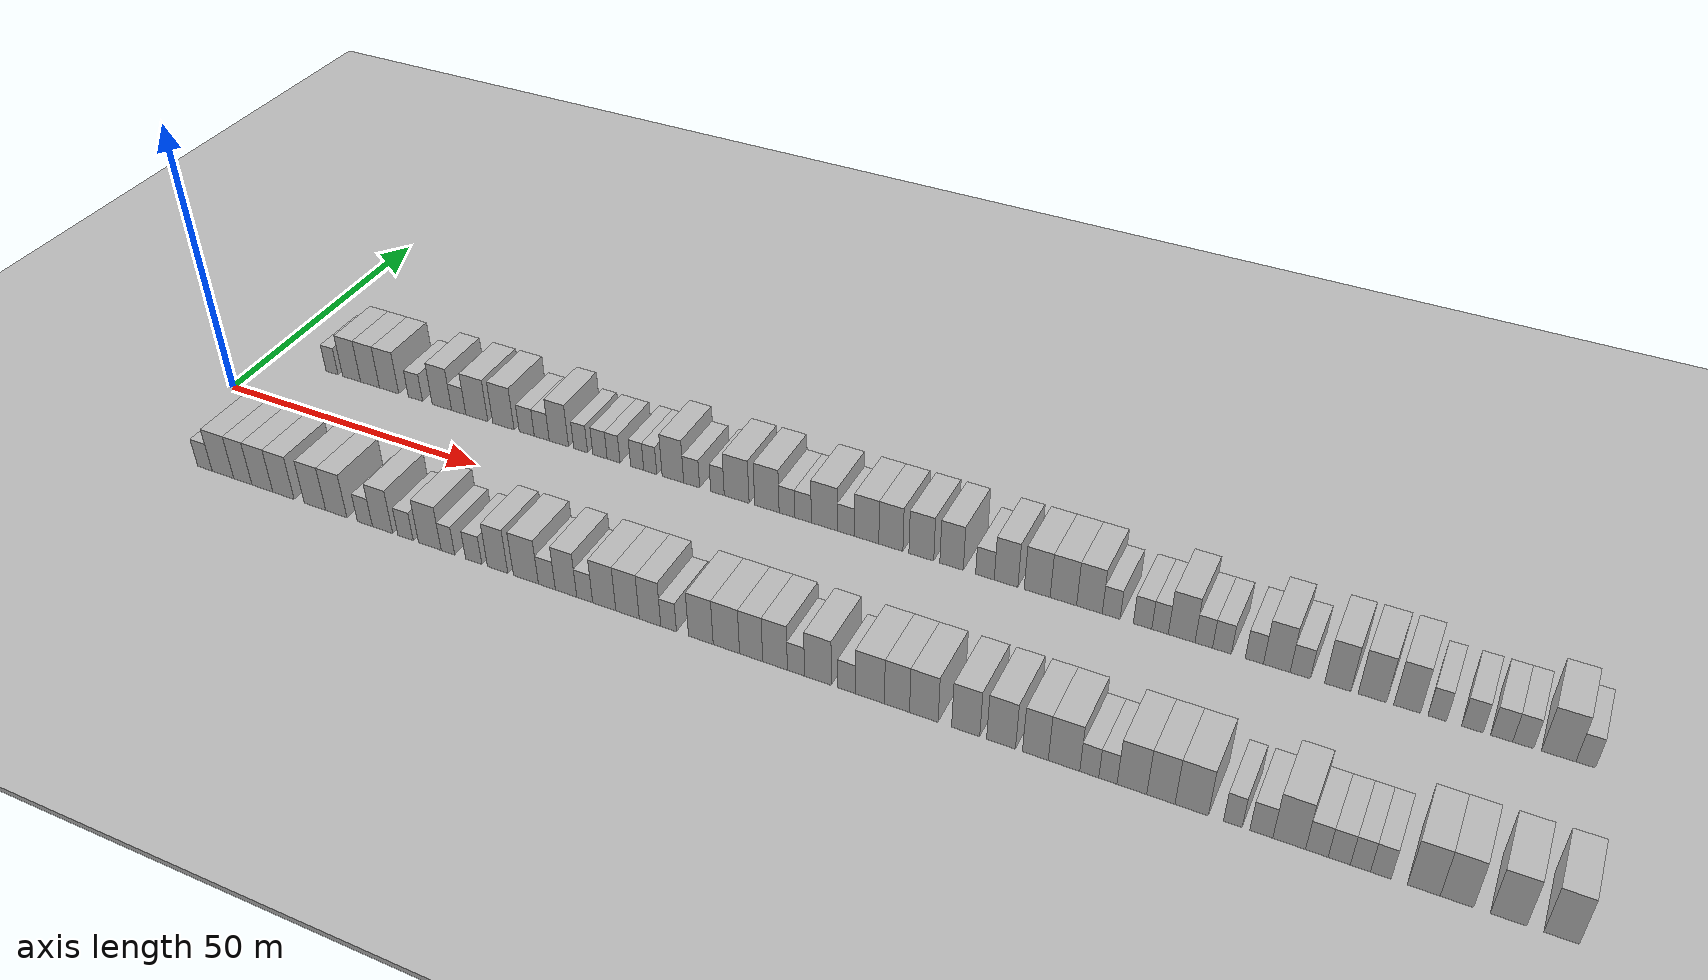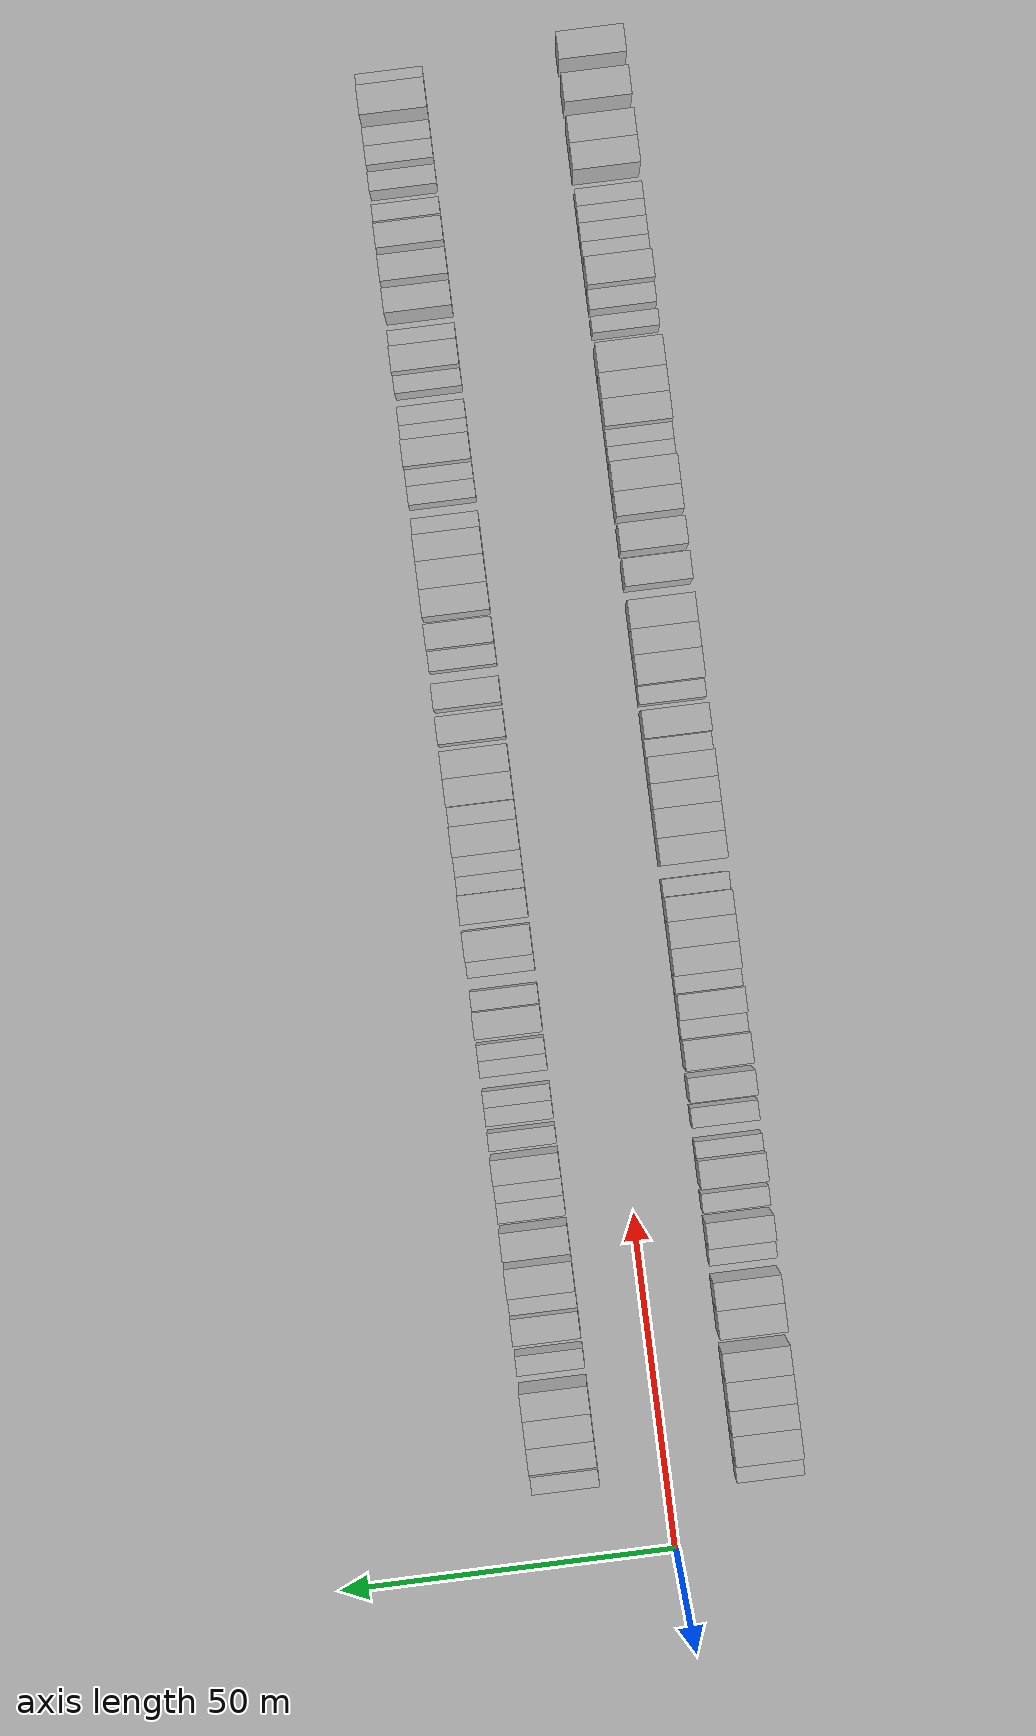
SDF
<?xml version="1.0" encoding="utf-8"?>

<sdf version="1.6">

   <world name="default">

      <gui fullscreen="0">

         <camera name="user_camera">

            <pose>-15 0 4.57585 0 0 0</pose>

            <view_controller>orbit</view_controller>

         </camera>

      </gui>

      <scene>

         <sky>

           <clouds>

             <speed>12</speed>

           </clouds>

         </sky>

         <ambient>0.4 0.4 0.4 1</ambient>

         <background>0.7 0.7 0.7 1</background>

         <shadows>1</shadows>

      </scene>

      <gravity>0 0 -9.8066</gravity>

      <magnetic_field>6e-06 2.3e-05 -4.2e-05</magnetic_field>

      <physics default="0" name="default_physics" type="ode">

         <ode>

            <solver>

               <type>quick</type>

               <iters>10</iters>

               <sor>1.0</sor>

               <use_dynamic_moi_rescaling>0</use_dynamic_moi_rescaling>

            </solver>

            <constraints>

               <cfm>0</cfm>

               <erp>0.2</erp>

               <contact_max_correcting_vel>100</contact_max_correcting_vel>

               <contact_surface_layer>0.001</contact_surface_layer>

            </constraints>

         </ode>

         <max_step_size>0.004</max_step_size>

         <real_time_factor>1</real_time_factor>

         <real_time_update_rate>250</real_time_update_rate>

      </physics>

      <light name="sun" type="directional">

         <cast_shadows>1</cast_shadows>

         <pose>0 0 10 0 0 0</pose>

         <diffuse>0.8 0.8 0.8 1</diffuse>

         <specular>0.2 0.2 0.2 1</specular>

         <attenuation>

            <range>1000</range>

            <constant>0.9</constant>

            <linear>0.01</linear>

            <quadratic>0.001</quadratic>

         </attenuation>

         <direction>-0.5 0.1 -0.9</direction>

      </light>

      <include>

         <name>ground_plane_1</name>

         <uri>model://HANNAS_ground_plane</uri>

         <pose>0 0 0  0 0 0</pose>

      </include>

      <include>

         <name>ground_plane_2</name>

         <uri>model://HANNAS_ground_plane</uri>

         <pose>100 0 0  0 0 0</pose>

      </include>

      <model name="building_1">

         <static>1</static>

         <pose frame="">13.2862 15.0000 0 0.000000 0.000000 1.570796</pose>

         <link name="link">

            <pose frame="">0 0 3.00 0 0 0</pose>

            <collision name="collision">

               <geometry>

                  <box>

                     <size>10.0000 2.5724 6.0000</size>

                  </box>

               </geometry>

               <max_contacts>10</max_contacts>

               <surface>

                  <contact>

                     <ode/>

                  </contact>

                  <bounce/>

                  <friction>

                     <torsional>

                        <ode/>

                     </torsional>

                     <ode/>

                  </friction>

               </surface>

            </collision>

            <visual name="visual">

               <cast_shadows>0</cast_shadows>

               <geometry>

                  <box>

                     <size>10.0000 2.5724 6.0000</size>

                  </box>

               </geometry>

               <material>

                  <script>

                     <uri>model://HANNAS_wall/materials/scripts</uri>

                     <uri>model://HANNAS_wall/materials/textures</uri>

                     <name>vrc/HANNAS_wall</name>

                  </script>

               </material>

            </visual>

            <self_collide>0</self_collide>

            <enable_wind>0</enable_wind>

            <kinematic>0</kinematic>

         </link>

      </model>

      <model name="building_2">

         <static>1</static>

         <pose frame="">17.4752 15.0000 0 0.000000 0.000000 1.570796</pose>

         <link name="link">

            <pose frame="">0 0 4.50 0 0 0</pose>

            <collision name="collision">

               <geometry>

                  <box>

                     <size>10.0000 3.8055 9.0000</size>

                  </box>

               </geometry>

               <max_contacts>10</max_contacts>

               <surface>

                  <contact>

                     <ode/>

                  </contact>

                  <bounce/>

                  <friction>

                     <torsional>

                        <ode/>

                     </torsional>

                     <ode/>

                  </friction>

               </surface>

            </collision>

            <visual name="visual">

               <cast_shadows>0</cast_shadows>

               <geometry>

                  <box>

                     <size>10.0000 3.8055 9.0000</size>

                  </box>

               </geometry>

               <material>

                  <script>

                     <uri>model://HANNAS_wall/materials/scripts</uri>

                     <uri>model://HANNAS_wall/materials/textures</uri>

                     <name>vrc/HANNAS_wall</name>

                  </script>

               </material>

            </visual>

            <self_collide>0</self_collide>

            <enable_wind>0</enable_wind>

            <kinematic>0</kinematic>

         </link>

      </model>

      <model name="building_3">

         <static>1</static>

         <pose frame="">21.3710 15.0000 0 0.000000 0.000000 1.570796</pose>

         <link name="link">

            <pose frame="">0 0 4.50 0 0 0</pose>

            <collision name="collision">

               <geometry>

                  <box>

                     <size>10.0000 3.9862 9.0000</size>

                  </box>

               </geometry>

               <max_contacts>10</max_contacts>

               <surface>

                  <contact>

                     <ode/>

                  </contact>

                  <bounce/>

                  <friction>

                     <torsional>

                        <ode/>

                     </torsional>

                     <ode/>

                  </friction>

               </surface>

            </collision>

            <visual name="visual">

               <cast_shadows>0</cast_shadows>

               <geometry>

                  <box>

                     <size>10.0000 3.9862 9.0000</size>

                  </box>

               </geometry>

               <material>

                  <script>

                     <uri>model://HANNAS_wall/materials/scripts</uri>

                     <uri>model://HANNAS_wall/materials/textures</uri>

                     <name>vrc/HANNAS_wall</name>

                  </script>

               </material>

            </visual>

            <self_collide>0</self_collide>

            <enable_wind>0</enable_wind>

            <kinematic>0</kinematic>

         </link>

      </model>

      <model name="building_4">

         <static>1</static>

         <pose frame="">25.3962 15.0000 0 0.000000 0.000000 1.570796</pose>

         <link name="link">

            <pose frame="">0 0 4.50 0 0 0</pose>

            <collision name="collision">

               <geometry>

                  <box>

                     <size>10.0000 4.0641 9.0000</size>

                  </box>

               </geometry>

               <max_contacts>10</max_contacts>

               <surface>

                  <contact>

                     <ode/>

                  </contact>

                  <bounce/>

                  <friction>

                     <torsional>

                        <ode/>

                     </torsional>

                     <ode/>

                  </friction>

               </surface>

            </collision>

            <visual name="visual">

               <cast_shadows>0</cast_shadows>

               <geometry>

                  <box>

                     <size>10.0000 4.0641 9.0000</size>

                  </box>

               </geometry>

               <material>

                  <script>

                     <uri>model://HANNAS_wall/materials/scripts</uri>

                     <uri>model://HANNAS_wall/materials/textures</uri>

                     <name>vrc/HANNAS_wall</name>

                  </script>

               </material>

            </visual>

            <self_collide>0</self_collide>

            <enable_wind>0</enable_wind>

            <kinematic>0</kinematic>

         </link>

      </model>

      <model name="building_5">

         <static>1</static>

         <pose frame="">30.8911 15.0000 0 0.000000 0.000000 1.570796</pose>

         <link name="link">

            <pose frame="">0 0 3.00 0 0 0</pose>

            <collision name="collision">

               <geometry>

                  <box>

                     <size>10.0000 2.9257 6.0000</size>

                  </box>

               </geometry>

               <max_contacts>10</max_contacts>

               <surface>

                  <contact>

                     <ode/>

                  </contact>

                  <bounce/>

                  <friction>

                     <torsional>

                        <ode/>

                     </torsional>

                     <ode/>

                  </friction>

               </surface>

            </collision>

            <visual name="visual">

               <cast_shadows>0</cast_shadows>

               <geometry>

                  <box>

                     <size>10.0000 2.9257 6.0000</size>

                  </box>

               </geometry>

               <material>

                  <script>

                     <uri>model://HANNAS_wall/materials/scripts</uri>

                     <uri>model://HANNAS_wall/materials/textures</uri>

                     <name>vrc/HANNAS_wall</name>

                  </script>

               </material>

            </visual>

            <self_collide>0</self_collide>

            <enable_wind>0</enable_wind>

            <kinematic>0</kinematic>

         </link>

      </model>

      <model name="building_6">

         <static>1</static>

         <pose frame="">36.3340 15.0000 0 0.000000 0.000000 1.570796</pose>

         <link name="link">

            <pose frame="">0 0 4.50 0 0 0</pose>

            <collision name="collision">

               <geometry>

                  <box>

                     <size>10.0000 3.9601 9.0000</size>

                  </box>

               </geometry>

               <max_contacts>10</max_contacts>

               <surface>

                  <contact>

                     <ode/>

                  </contact>

                  <bounce/>

                  <friction>

                     <torsional>

                        <ode/>

                     </torsional>

                     <ode/>

                  </friction>

               </surface>

            </collision>

            <visual name="visual">

               <cast_shadows>0</cast_shadows>

               <geometry>

                  <box>

                     <size>10.0000 3.9601 9.0000</size>

                  </box>

               </geometry>

               <material>

                  <script>

                     <uri>model://HANNAS_wall/materials/scripts</uri>

                     <uri>model://HANNAS_wall/materials/textures</uri>

                     <name>vrc/HANNAS_wall</name>

                  </script>

               </material>

            </visual>

            <self_collide>0</self_collide>

            <enable_wind>0</enable_wind>

            <kinematic>0</kinematic>

         </link>

      </model>

      <model name="building_7">

         <static>1</static>

         <pose frame="">39.7516 15.0000 0 0.000000 0.000000 1.570796</pose>

         <link name="link">

            <pose frame="">0 0 3.00 0 0 0</pose>

            <collision name="collision">

               <geometry>

                  <box>

                     <size>10.0000 2.8751 6.0000</size>

                  </box>

               </geometry>

               <max_contacts>10</max_contacts>

               <surface>

                  <contact>

                     <ode/>

                  </contact>

                  <bounce/>

                  <friction>

                     <torsional>

                        <ode/>

                     </torsional>

                     <ode/>

                  </friction>

               </surface>

            </collision>

            <visual name="visual">

               <cast_shadows>0</cast_shadows>

               <geometry>

                  <box>

                     <size>10.0000 2.8751 6.0000</size>

                  </box>

               </geometry>

               <material>

                  <script>

                     <uri>model://HANNAS_wall/materials/scripts</uri>

                     <uri>model://HANNAS_wall/materials/textures</uri>

                     <name>vrc/HANNAS_wall</name>

                  </script>

               </material>

            </visual>

            <self_collide>0</self_collide>

            <enable_wind>0</enable_wind>

            <kinematic>0</kinematic>

         </link>

      </model>

      <model name="building_8">

         <static>1</static>

         <pose frame="">43.4057 15.0000 0 0.000000 0.000000 1.570796</pose>

         <link name="link">

            <pose frame="">0 0 4.50 0 0 0</pose>

            <collision name="collision">

               <geometry>

                  <box>

                     <size>10.0000 4.4330 9.0000</size>

                  </box>

               </geometry>

               <max_contacts>10</max_contacts>

               <surface>

                  <contact>

                     <ode/>

                  </contact>

                  <bounce/>

                  <friction>

                     <torsional>

                        <ode/>

                     </torsional>

                     <ode/>

                  </friction>

               </surface>

            </collision>

            <visual name="visual">

               <cast_shadows>0</cast_shadows>

               <geometry>

                  <box>

                     <size>10.0000 4.4330 9.0000</size>

                  </box>

               </geometry>

               <material>

                  <script>

                     <uri>model://HANNAS_wall/materials/scripts</uri>

                     <uri>model://HANNAS_wall/materials/textures</uri>

                     <name>vrc/HANNAS_wall</name>

                  </script>

               </material>

            </visual>

            <self_collide>0</self_collide>

            <enable_wind>0</enable_wind>

            <kinematic>0</kinematic>

         </link>

      </model>

      <model name="building_9">

         <static>1</static>

         <pose frame="">48.7348 15.0000 0 0.000000 0.000000 1.570796</pose>

         <link name="link">

            <pose frame="">0 0 4.50 0 0 0</pose>

            <collision name="collision">

               <geometry>

                  <box>

                     <size>10.0000 4.2253 9.0000</size>

                  </box>

               </geometry>

               <max_contacts>10</max_contacts>

               <surface>

                  <contact>

                     <ode/>

                  </contact>

                  <bounce/>

                  <friction>

                     <torsional>

                        <ode/>

                     </torsional>

                     <ode/>

                  </friction>

               </surface>

            </collision>

            <visual name="visual">

               <cast_shadows>0</cast_shadows>

               <geometry>

                  <box>

                     <size>10.0000 4.2253 9.0000</size>

                  </box>

               </geometry>

               <material>

                  <script>

                     <uri>model://HANNAS_wall/materials/scripts</uri>

                     <uri>model://HANNAS_wall/materials/textures</uri>

                     <name>vrc/HANNAS_wall</name>

                  </script>

               </material>

            </visual>

            <self_collide>0</self_collide>

            <enable_wind>0</enable_wind>

            <kinematic>0</kinematic>

         </link>

      </model>

      <model name="building_10">

         <static>1</static>

         <pose frame="">53.3366 15.0000 0 0.000000 0.000000 1.570796</pose>

         <link name="link">

            <pose frame="">0 0 3.00 0 0 0</pose>

            <collision name="collision">

               <geometry>

                  <box>

                     <size>10.0000 2.9783 6.0000</size>

                  </box>

               </geometry>

               <max_contacts>10</max_contacts>

               <surface>

                  <contact>

                     <ode/>

                  </contact>

                  <bounce/>

                  <friction>

                     <torsional>

                        <ode/>

                     </torsional>

                     <ode/>

                  </friction>

               </surface>

            </collision>

            <visual name="visual">

               <cast_shadows>0</cast_shadows>

               <geometry>

                  <box>

                     <size>10.0000 2.9783 6.0000</size>

                  </box>

               </geometry>

               <material>

                  <script>

                     <uri>model://HANNAS_wall/materials/scripts</uri>

                     <uri>model://HANNAS_wall/materials/textures</uri>

                     <name>vrc/HANNAS_wall</name>

                  </script>

               </material>

            </visual>

            <self_collide>0</self_collide>

            <enable_wind>0</enable_wind>

            <kinematic>0</kinematic>

         </link>

      </model>

      <model name="building_11">

         <static>1</static>

         <pose frame="">56.2876 15.0000 0 0.000000 0.000000 1.570796</pose>

         <link name="link">

            <pose frame="">0 0 3.00 0 0 0</pose>

            <collision name="collision">

               <geometry>

                  <box>

                     <size>10.0000 2.9236 6.0000</size>

                  </box>

               </geometry>

               <max_contacts>10</max_contacts>

               <surface>

                  <contact>

                     <ode/>

                  </contact>

                  <bounce/>

                  <friction>

                     <torsional>

                        <ode/>

                     </torsional>

                     <ode/>

                  </friction>

               </surface>

            </collision>

            <visual name="visual">

               <cast_shadows>0</cast_shadows>

               <geometry>

                  <box>

                     <size>10.0000 2.9236 6.0000</size>

                  </box>

               </geometry>

               <material>

                  <script>

                     <uri>model://HANNAS_wall/materials/scripts</uri>

                     <uri>model://HANNAS_wall/materials/textures</uri>

                     <name>vrc/HANNAS_wall</name>

                  </script>

               </material>

            </visual>

            <self_collide>0</self_collide>

            <enable_wind>0</enable_wind>

            <kinematic>0</kinematic>

         </link>

      </model>

      <model name="building_12">

         <static>1</static>

         <pose frame="">59.6168 15.0000 0 0.000000 0.000000 1.570796</pose>

         <link name="link">

            <pose frame="">0 0 4.50 0 0 0</pose>

            <collision name="collision">

               <geometry>

                  <box>

                     <size>10.0000 3.7350 9.0000</size>

                  </box>

               </geometry>

               <max_contacts>10</max_contacts>

               <surface>

                  <contact>

                     <ode/>

                  </contact>

                  <bounce/>

                  <friction>

                     <torsional>

                        <ode/>

                     </torsional>

                     <ode/>

                  </friction>

               </surface>

            </collision>

            <visual name="visual">

               <cast_shadows>0</cast_shadows>

               <geometry>

                  <box>

                     <size>10.0000 3.7350 9.0000</size>

                  </box>

               </geometry>

               <material>

                  <script>

                     <uri>model://HANNAS_wall/materials/scripts</uri>

                     <uri>model://HANNAS_wall/materials/textures</uri>

                     <name>vrc/HANNAS_wall</name>

                  </script>

               </material>

            </visual>

            <self_collide>0</self_collide>

            <enable_wind>0</enable_wind>

            <kinematic>0</kinematic>

         </link>

      </model>

      <model name="building_13">

         <static>1</static>

         <pose frame="">63.8142 15.0000 0 0.000000 0.000000 1.570796</pose>

         <link name="link">

            <pose frame="">0 0 3.00 0 0 0</pose>

            <collision name="collision">

               <geometry>

                  <box>

                     <size>10.0000 2.6598 6.0000</size>

                  </box>

               </geometry>

               <max_contacts>10</max_contacts>

               <surface>

                  <contact>

                     <ode/>

                  </contact>

                  <bounce/>

                  <friction>

                     <torsional>

                        <ode/>

                     </torsional>

                     <ode/>

                  </friction>

               </surface>

            </collision>

            <visual name="visual">

               <cast_shadows>0</cast_shadows>

               <geometry>

                  <box>

                     <size>10.0000 2.6598 6.0000</size>

                  </box>

               </geometry>

               <material>

                  <script>

                     <uri>model://HANNAS_wall/materials/scripts</uri>

                     <uri>model://HANNAS_wall/materials/textures</uri>

                     <name>vrc/HANNAS_wall</name>

                  </script>

               </material>

            </visual>

            <self_collide>0</self_collide>

            <enable_wind>0</enable_wind>

            <kinematic>0</kinematic>

         </link>

      </model>

      <model name="building_14">

         <static>1</static>

         <pose frame="">67.4996 15.0000 0 0.000000 0.000000 1.570796</pose>

         <link name="link">

            <pose frame="">0 0 3.00 0 0 0</pose>

            <collision name="collision">

               <geometry>

                  <box>

                     <size>10.0000 2.7109 6.0000</size>

                  </box>

               </geometry>

               <max_contacts>10</max_contacts>

               <surface>

                  <contact>

                     <ode/>

                  </contact>

                  <bounce/>

                  <friction>

                     <torsional>

                        <ode/>

                     </torsional>

                     <ode/>

                  </friction>

               </surface>

            </collision>

            <visual name="visual">

               <cast_shadows>0</cast_shadows>

               <geometry>

                  <box>

                     <size>10.0000 2.7109 6.0000</size>

                  </box>

               </geometry>

               <material>

                  <script>

                     <uri>model://HANNAS_wall/materials/scripts</uri>

                     <uri>model://HANNAS_wall/materials/textures</uri>

                     <name>vrc/HANNAS_wall</name>

                  </script>

               </material>

            </visual>

            <self_collide>0</self_collide>

            <enable_wind>0</enable_wind>

            <kinematic>0</kinematic>

         </link>

      </model>

      <model name="building_15">

         <static>1</static>

         <pose frame="">70.0767 15.0000 0 0.000000 0.000000 1.570796</pose>

         <link name="link">

            <pose frame="">0 0 3.00 0 0 0</pose>

            <collision name="collision">

               <geometry>

                  <box>

                     <size>10.0000 2.4434 6.0000</size>

                  </box>

               </geometry>

               <max_contacts>10</max_contacts>

               <surface>

                  <contact>

                     <ode/>

                  </contact>

                  <bounce/>

                  <friction>

                     <torsional>

                        <ode/>

                     </torsional>

                     <ode/>

                  </friction>

               </surface>

            </collision>

            <visual name="visual">

               <cast_shadows>0</cast_shadows>

               <geometry>

                  <box>

                     <size>10.0000 2.4434 6.0000</size>

                  </box>

               </geometry>

               <material>

                  <script>

                     <uri>model://HANNAS_wall/materials/scripts</uri>

                     <uri>model://HANNAS_wall/materials/textures</uri>

                     <name>vrc/HANNAS_wall</name>

                  </script>

               </material>

            </visual>

            <self_collide>0</self_collide>

            <enable_wind>0</enable_wind>

            <kinematic>0</kinematic>

         </link>

      </model>

      <model name="building_16">

         <static>1</static>

         <pose frame="">74.5183 15.0000 0 0.000000 0.000000 1.570796</pose>

         <link name="link">

            <pose frame="">0 0 3.00 0 0 0</pose>

            <collision name="collision">

               <geometry>

                  <box>

                     <size>10.0000 2.4397 6.0000</size>

                  </box>

               </geometry>

               <max_contacts>10</max_contacts>

               <surface>

                  <contact>

                     <ode/>

                  </contact>

                  <bounce/>

                  <friction>

                     <torsional>

                        <ode/>

                     </torsional>

                     <ode/>

                  </friction>

               </surface>

            </collision>

            <visual name="visual">

               <cast_shadows>0</cast_shadows>

               <geometry>

                  <box>

                     <size>10.0000 2.4397 6.0000</size>

                  </box>

               </geometry>

               <material>

                  <script>

                     <uri>model://HANNAS_wall/materials/scripts</uri>

                     <uri>model://HANNAS_wall/materials/textures</uri>

                     <name>vrc/HANNAS_wall</name>

                  </script>

               </material>

            </visual>

            <self_collide>0</self_collide>

            <enable_wind>0</enable_wind>

            <kinematic>0</kinematic>

         </link>

      </model>

      <model name="building_17">

         <static>1</static>

         <pose frame="">76.9490 15.0000 0 0.000000 0.000000 1.570796</pose>

         <link name="link">

            <pose frame="">0 0 3.00 0 0 0</pose>

            <collision name="collision">

               <geometry>

                  <box>

                     <size>10.0000 2.4216 6.0000</size>

                  </box>

               </geometry>

               <max_contacts>10</max_contacts>

               <surface>

                  <contact>

                     <ode/>

                  </contact>

                  <bounce/>

                  <friction>

                     <torsional>

                        <ode/>

                     </torsional>

                     <ode/>

                  </friction>

               </surface>

            </collision>

            <visual name="visual">

               <cast_shadows>0</cast_shadows>

               <geometry>

                  <box>

                     <size>10.0000 2.4216 6.0000</size>

                  </box>

               </geometry>

               <material>

                  <script>

                     <uri>model://HANNAS_wall/materials/scripts</uri>

                     <uri>model://HANNAS_wall/materials/textures</uri>

                     <name>vrc/HANNAS_wall</name>

                  </script>

               </material>

            </visual>

            <self_collide>0</self_collide>

            <enable_wind>0</enable_wind>

            <kinematic>0</kinematic>

         </link>

      </model>

      <model name="building_18">

         <static>1</static>

         <pose frame="">81.1411 15.0000 0 0.000000 0.000000 1.570796</pose>

         <link name="link">

            <pose frame="">0 0 4.50 0 0 0</pose>

            <collision name="collision">

               <geometry>

                  <box>

                     <size>10.0000 3.9626 9.0000</size>

                  </box>

               </geometry>

               <max_contacts>10</max_contacts>

               <surface>

                  <contact>

                     <ode/>

                  </contact>

                  <bounce/>

                  <friction>

                     <torsional>

                        <ode/>

                     </torsional>

                     <ode/>

                  </friction>

               </surface>

            </collision>

            <visual name="visual">

               <cast_shadows>0</cast_shadows>

               <geometry>

                  <box>

                     <size>10.0000 3.9626 9.0000</size>

                  </box>

               </geometry>

               <material>

                  <script>

                     <uri>model://HANNAS_wall/materials/scripts</uri>

                     <uri>model://HANNAS_wall/materials/textures</uri>

                     <name>vrc/HANNAS_wall</name>

                  </script>

               </material>

            </visual>

            <self_collide>0</self_collide>

            <enable_wind>0</enable_wind>

            <kinematic>0</kinematic>

         </link>

      </model>

      <model name="building_19">

         <static>1</static>

         <pose frame="">84.5773 15.0000 0 0.000000 0.000000 1.570796</pose>

         <link name="link">

            <pose frame="">0 0 3.00 0 0 0</pose>

            <collision name="collision">

               <geometry>

                  <box>

                     <size>10.0000 2.9098 6.0000</size>

                  </box>

               </geometry>

               <max_contacts>10</max_contacts>

               <surface>

                  <contact>

                     <ode/>

                  </contact>

                  <bounce/>

                  <friction>

                     <torsional>

                        <ode/>

                     </torsional>

                     <ode/>

                  </friction>

               </surface>

            </collision>

            <visual name="visual">

               <cast_shadows>0</cast_shadows>

               <geometry>

                  <box>

                     <size>10.0000 2.9098 6.0000</size>

                  </box>

               </geometry>

               <material>

                  <script>

                     <uri>model://HANNAS_wall/materials/scripts</uri>

                     <uri>model://HANNAS_wall/materials/textures</uri>

                     <name>vrc/HANNAS_wall</name>

                  </script>

               </material>

            </visual>

            <self_collide>0</self_collide>

            <enable_wind>0</enable_wind>

            <kinematic>0</kinematic>

         </link>

      </model>

      <model name="building_20">

         <static>1</static>

         <pose frame="">89.2566 15.0000 0 0.000000 0.000000 1.570796</pose>

         <link name="link">

            <pose frame="">0 0 3.00 0 0 0</pose>

            <collision name="collision">

               <geometry>

                  <box>

                     <size>10.0000 2.4487 6.0000</size>

                  </box>

               </geometry>

               <max_contacts>10</max_contacts>

               <surface>

                  <contact>

                     <ode/>

                  </contact>

                  <bounce/>

                  <friction>

                     <torsional>

                        <ode/>

                     </torsional>

                     <ode/>

                  </friction>

               </surface>

            </collision>

            <visual name="visual">

               <cast_shadows>0</cast_shadows>

               <geometry>

                  <box>

                     <size>10.0000 2.4487 6.0000</size>

                  </box>

               </geometry>

               <material>

                  <script>

                     <uri>model://HANNAS_wall/materials/scripts</uri>

                     <uri>model://HANNAS_wall/materials/textures</uri>

                     <name>vrc/HANNAS_wall</name>

                  </script>

               </material>

            </visual>

            <self_collide>0</self_collide>

            <enable_wind>0</enable_wind>

            <kinematic>0</kinematic>

         </link>

      </model>

      <model name="building_21">

         <static>1</static>

         <pose frame="">92.7052 15.0000 0 0.000000 0.000000 1.570796</pose>

         <link name="link">

            <pose frame="">0 0 4.50 0 0 0</pose>

            <collision name="collision">

               <geometry>

                  <box>

                     <size>10.0000 4.4486 9.0000</size>

                  </box>

               </geometry>

               <max_contacts>10</max_contacts>

               <surface>

                  <contact>

                     <ode/>

                  </contact>

                  <bounce/>

                  <friction>

                     <torsional>

                        <ode/>

                     </torsional>

                     <ode/>

                  </friction>

               </surface>

            </collision>

            <visual name="visual">

               <cast_shadows>0</cast_shadows>

               <geometry>

                  <box>

                     <size>10.0000 4.4486 9.0000</size>

                  </box>

               </geometry>

               <material>

                  <script>

                     <uri>model://HANNAS_wall/materials/scripts</uri>

                     <uri>model://HANNAS_wall/materials/textures</uri>

                     <name>vrc/HANNAS_wall</name>

                  </script>

               </material>

            </visual>

            <self_collide>0</self_collide>

            <enable_wind>0</enable_wind>

            <kinematic>0</kinematic>

         </link>

      </model>

      <model name="building_22">

         <static>1</static>

         <pose frame="">98.0822 15.0000 0 0.000000 0.000000 1.570796</pose>

         <link name="link">

            <pose frame="">0 0 4.50 0 0 0</pose>

            <collision name="collision">

               <geometry>

                  <box>

                     <size>10.0000 4.3055 9.0000</size>

                  </box>

               </geometry>

               <max_contacts>10</max_contacts>

               <surface>

                  <contact>

                     <ode/>

                  </contact>

                  <bounce/>

                  <friction>

                     <torsional>

                        <ode/>

                     </torsional>

                     <ode/>

                  </friction>

               </surface>

            </collision>

            <visual name="visual">

               <cast_shadows>0</cast_shadows>

               <geometry>

                  <box>

                     <size>10.0000 4.3055 9.0000</size>

                  </box>

               </geometry>

               <material>

                  <script>

                     <uri>model://HANNAS_wall/materials/scripts</uri>

                     <uri>model://HANNAS_wall/materials/textures</uri>

                     <name>vrc/HANNAS_wall</name>

                  </script>

               </material>

            </visual>

            <self_collide>0</self_collide>

            <enable_wind>0</enable_wind>

            <kinematic>0</kinematic>

         </link>

      </model>

      <model name="building_23">

         <static>1</static>

         <pose frame="">101.5895 15.0000 0 0.000000 0.000000 1.570796</pose>

         <link name="link">

            <pose frame="">0 0 3.00 0 0 0</pose>

            <collision name="collision">

               <geometry>

                  <box>

                     <size>10.0000 2.7089 6.0000</size>

                  </box>

               </geometry>

               <max_contacts>10</max_contacts>

               <surface>

                  <contact>

                     <ode/>

                  </contact>

                  <bounce/>

                  <friction>

                     <torsional>

                        <ode/>

                     </torsional>

                     <ode/>

                  </friction>

               </surface>

            </collision>

            <visual name="visual">

               <cast_shadows>0</cast_shadows>

               <geometry>

                  <box>

                     <size>10.0000 2.7089 6.0000</size>

                  </box>

               </geometry>

               <material>

                  <script>

                     <uri>model://HANNAS_wall/materials/scripts</uri>

                     <uri>model://HANNAS_wall/materials/textures</uri>

                     <name>vrc/HANNAS_wall</name>

                  </script>

               </material>

            </visual>

            <self_collide>0</self_collide>

            <enable_wind>0</enable_wind>

            <kinematic>0</kinematic>

         </link>

      </model>

      <model name="building_24">

         <static>1</static>

         <pose frame="">104.3950 15.0000 0 0.000000 0.000000 1.570796</pose>

         <link name="link">

            <pose frame="">0 0 3.00 0 0 0</pose>

            <collision name="collision">

               <geometry>

                  <box>

                     <size>10.0000 2.9022 6.0000</size>

                  </box>

               </geometry>

               <max_contacts>10</max_contacts>

               <surface>

                  <contact>

                     <ode/>

                  </contact>

                  <bounce/>

                  <friction>

                     <torsional>

                        <ode/>

                     </torsional>

                     <ode/>

                  </friction>

               </surface>

            </collision>

            <visual name="visual">

               <cast_shadows>0</cast_shadows>

               <geometry>

                  <box>

                     <size>10.0000 2.9022 6.0000</size>

                  </box>

               </geometry>

               <material>

                  <script>

                     <uri>model://HANNAS_wall/materials/scripts</uri>

                     <uri>model://HANNAS_wall/materials/textures</uri>

                     <name>vrc/HANNAS_wall</name>

                  </script>

               </material>

            </visual>

            <self_collide>0</self_collide>

            <enable_wind>0</enable_wind>

            <kinematic>0</kinematic>

         </link>

      </model>

      <model name="building_25">

         <static>1</static>

         <pose frame="">108.0881 15.0000 0 0.000000 0.000000 1.570796</pose>

         <link name="link">

            <pose frame="">0 0 4.50 0 0 0</pose>

            <collision name="collision">

               <geometry>

                  <box>

                     <size>10.0000 4.4841 9.0000</size>

                  </box>

               </geometry>

               <max_contacts>10</max_contacts>

               <surface>

                  <contact>

                     <ode/>

                  </contact>

                  <bounce/>

                  <friction>

                     <torsional>

                        <ode/>

                     </torsional>

                     <ode/>

                  </friction>

               </surface>

            </collision>

            <visual name="visual">

               <cast_shadows>0</cast_shadows>

               <geometry>

                  <box>

                     <size>10.0000 4.4841 9.0000</size>

                  </box>

               </geometry>

               <material>

                  <script>

                     <uri>model://HANNAS_wall/materials/scripts</uri>

                     <uri>model://HANNAS_wall/materials/textures</uri>

                     <name>vrc/HANNAS_wall</name>

                  </script>

               </material>

            </visual>

            <self_collide>0</self_collide>

            <enable_wind>0</enable_wind>

            <kinematic>0</kinematic>

         </link>

      </model>

      <model name="building_26">

         <static>1</static>

         <pose frame="">111.7850 15.0000 0 0.000000 0.000000 1.570796</pose>

         <link name="link">

            <pose frame="">0 0 3.00 0 0 0</pose>

            <collision name="collision">

               <geometry>

                  <box>

                     <size>10.0000 2.9097 6.0000</size>

                  </box>

               </geometry>

               <max_contacts>10</max_contacts>

               <surface>

                  <contact>

                     <ode/>

                  </contact>

                  <bounce/>

                  <friction>

                     <torsional>

                        <ode/>

                     </torsional>

                     <ode/>

                  </friction>

               </surface>

            </collision>

            <visual name="visual">

               <cast_shadows>0</cast_shadows>

               <geometry>

                  <box>

                     <size>10.0000 2.9097 6.0000</size>

                  </box>

               </geometry>

               <material>

                  <script>

                     <uri>model://HANNAS_wall/materials/scripts</uri>

                     <uri>model://HANNAS_wall/materials/textures</uri>

                     <name>vrc/HANNAS_wall</name>

                  </script>

               </material>

            </visual>

            <self_collide>0</self_collide>

            <enable_wind>0</enable_wind>

            <kinematic>0</kinematic>

         </link>

      </model>

      <model name="building_27">

         <static>1</static>

         <pose frame="">115.3012 15.0000 0 0.000000 0.000000 1.570796</pose>

         <link name="link">

            <pose frame="">0 0 4.50 0 0 0</pose>

            <collision name="collision">

               <geometry>

                  <box>

                     <size>10.0000 4.1226 9.0000</size>

                  </box>

               </geometry>

               <max_contacts>10</max_contacts>

               <surface>

                  <contact>

                     <ode/>

                  </contact>

                  <bounce/>

                  <friction>

                     <torsional>

                        <ode/>

                     </torsional>

                     <ode/>

                  </friction>

               </surface>

            </collision>

            <visual name="visual">

               <cast_shadows>0</cast_shadows>

               <geometry>

                  <box>

                     <size>10.0000 4.1226 9.0000</size>

                  </box>

               </geometry>

               <material>

                  <script>

                     <uri>model://HANNAS_wall/materials/scripts</uri>

                     <uri>model://HANNAS_wall/materials/textures</uri>

                     <name>vrc/HANNAS_wall</name>

                  </script>

               </material>

            </visual>

            <self_collide>0</self_collide>

            <enable_wind>0</enable_wind>

            <kinematic>0</kinematic>

         </link>

      </model>

      <model name="building_28">

         <static>1</static>

         <pose frame="">119.3822 15.0000 0 0.000000 0.000000 1.570796</pose>

         <link name="link">

            <pose frame="">0 0 4.50 0 0 0</pose>

            <collision name="collision">

               <geometry>

                  <box>

                     <size>10.0000 4.0395 9.0000</size>

                  </box>

               </geometry>

               <max_contacts>10</max_contacts>

               <surface>

                  <contact>

                     <ode/>

                  </contact>

                  <bounce/>

                  <friction>

                     <torsional>

                        <ode/>

                     </torsional>

                     <ode/>

                  </friction>

               </surface>

            </collision>

            <visual name="visual">

               <cast_shadows>0</cast_shadows>

               <geometry>

                  <box>

                     <size>10.0000 4.0395 9.0000</size>

                  </box>

               </geometry>

               <material>

                  <script>

                     <uri>model://HANNAS_wall/materials/scripts</uri>

                     <uri>model://HANNAS_wall/materials/textures</uri>

                     <name>vrc/HANNAS_wall</name>

                  </script>

               </material>

            </visual>

            <self_collide>0</self_collide>

            <enable_wind>0</enable_wind>

            <kinematic>0</kinematic>

         </link>

      </model>

      <model name="building_29">

         <static>1</static>

         <pose frame="">124.4516 15.0000 0 0.000000 0.000000 1.570796</pose>

         <link name="link">

            <pose frame="">0 0 4.50 0 0 0</pose>

            <collision name="collision">

               <geometry>

                  <box>

                     <size>10.0000 4.0994 9.0000</size>

                  </box>

               </geometry>

               <max_contacts>10</max_contacts>

               <surface>

                  <contact>

                     <ode/>

                  </contact>

                  <bounce/>

                  <friction>

                     <torsional>

                        <ode/>

                     </torsional>

                     <ode/>

                  </friction>

               </surface>

            </collision>

            <visual name="visual">

               <cast_shadows>0</cast_shadows>

               <geometry>

                  <box>

                     <size>10.0000 4.0994 9.0000</size>

                  </box>

               </geometry>

               <material>

                  <script>

                     <uri>model://HANNAS_wall/materials/scripts</uri>

                     <uri>model://HANNAS_wall/materials/textures</uri>

                     <name>vrc/HANNAS_wall</name>

                  </script>

               </material>

            </visual>

            <self_collide>0</self_collide>

            <enable_wind>0</enable_wind>

            <kinematic>0</kinematic>

         </link>

      </model>

      <model name="building_30">

         <static>1</static>

         <pose frame="">129.4214 15.0000 0 0.000000 0.000000 1.570796</pose>

         <link name="link">

            <pose frame="">0 0 4.50 0 0 0</pose>

            <collision name="collision">

               <geometry>

                  <box>

                     <size>10.0000 3.8402 9.0000</size>

                  </box>

               </geometry>

               <max_contacts>10</max_contacts>

               <surface>

                  <contact>

                     <ode/>

                  </contact>

                  <bounce/>

                  <friction>

                     <torsional>

                        <ode/>

                     </torsional>

                     <ode/>

                  </friction>

               </surface>

            </collision>

            <visual name="visual">

               <cast_shadows>0</cast_shadows>

               <geometry>

                  <box>

                     <size>10.0000 3.8402 9.0000</size>

                  </box>

               </geometry>

               <material>

                  <script>

                     <uri>model://HANNAS_wall/materials/scripts</uri>

                     <uri>model://HANNAS_wall/materials/textures</uri>

                     <name>vrc/HANNAS_wall</name>

                  </script>

               </material>

            </visual>

            <self_collide>0</self_collide>

            <enable_wind>0</enable_wind>

            <kinematic>0</kinematic>

         </link>

      </model>

      <model name="building_31">

         <static>1</static>

         <pose frame="">134.8365 15.0000 0 0.000000 0.000000 1.570796</pose>

         <link name="link">

            <pose frame="">0 0 3.00 0 0 0</pose>

            <collision name="collision">

               <geometry>

                  <box>

                     <size>10.0000 2.9901 6.0000</size>

                  </box>

               </geometry>

               <max_contacts>10</max_contacts>

               <surface>

                  <contact>

                     <ode/>

                  </contact>

                  <bounce/>

                  <friction>

                     <torsional>

                        <ode/>

                     </torsional>

                     <ode/>

                  </friction>

               </surface>

            </collision>

            <visual name="visual">

               <cast_shadows>0</cast_shadows>

               <geometry>

                  <box>

                     <size>10.0000 2.9901 6.0000</size>

                  </box>

               </geometry>

               <material>

                  <script>

                     <uri>model://HANNAS_wall/materials/scripts</uri>

                     <uri>model://HANNAS_wall/materials/textures</uri>

                     <name>vrc/HANNAS_wall</name>

                  </script>

               </material>

            </visual>

            <self_collide>0</self_collide>

            <enable_wind>0</enable_wind>

            <kinematic>0</kinematic>

         </link>

      </model>

      <model name="building_32">

         <static>1</static>

         <pose frame="">138.2175 15.0000 0 0.000000 0.000000 1.570796</pose>

         <link name="link">

            <pose frame="">0 0 4.50 0 0 0</pose>

            <collision name="collision">

               <geometry>

                  <box>

                     <size>10.0000 3.7719 9.0000</size>

                  </box>

               </geometry>

               <max_contacts>10</max_contacts>

               <surface>

                  <contact>

                     <ode/>

                  </contact>

                  <bounce/>

                  <friction>

                     <torsional>

                        <ode/>

                     </torsional>

                     <ode/>

                  </friction>

               </surface>

            </collision>

            <visual name="visual">

               <cast_shadows>0</cast_shadows>

               <geometry>

                  <box>

                     <size>10.0000 3.7719 9.0000</size>

                  </box>

               </geometry>

               <material>

                  <script>

                     <uri>model://HANNAS_wall/materials/scripts</uri>

                     <uri>model://HANNAS_wall/materials/textures</uri>

                     <name>vrc/HANNAS_wall</name>

                  </script>

               </material>

            </visual>

            <self_collide>0</self_collide>

            <enable_wind>0</enable_wind>

            <kinematic>0</kinematic>

         </link>

      </model>

      <model name="building_33">

         <static>1</static>

         <pose frame="">143.1482 15.0000 0 0.000000 0.000000 1.570796</pose>

         <link name="link">

            <pose frame="">0 0 4.50 0 0 0</pose>

            <collision name="collision">

               <geometry>

                  <box>

                     <size>10.0000 4.0895 9.0000</size>

                  </box>

               </geometry>

               <max_contacts>10</max_contacts>

               <surface>

                  <contact>

                     <ode/>

                  </contact>

                  <bounce/>

                  <friction>

                     <torsional>

                        <ode/>

                     </torsional>

                     <ode/>

                  </friction>

               </surface>

            </collision>

            <visual name="visual">

               <cast_shadows>0</cast_shadows>

               <geometry>

                  <box>

                     <size>10.0000 4.0895 9.0000</size>

                  </box>

               </geometry>

               <material>

                  <script>

                     <uri>model://HANNAS_wall/materials/scripts</uri>

                     <uri>model://HANNAS_wall/materials/textures</uri>

                     <name>vrc/HANNAS_wall</name>

                  </script>

               </material>

            </visual>

            <self_collide>0</self_collide>

            <enable_wind>0</enable_wind>

            <kinematic>0</kinematic>

         </link>

      </model>

      <model name="building_34">

         <static>1</static>

         <pose frame="">147.2556 15.0000 0 0.000000 0.000000 1.570796</pose>

         <link name="link">

            <pose frame="">0 0 4.50 0 0 0</pose>

            <collision name="collision">

               <geometry>

                  <box>

                     <size>10.0000 4.1252 9.0000</size>

                  </box>

               </geometry>

               <max_contacts>10</max_contacts>

               <surface>

                  <contact>

                     <ode/>

                  </contact>

                  <bounce/>

                  <friction>

                     <torsional>

                        <ode/>

                     </torsional>

                     <ode/>

                  </friction>

               </surface>

            </collision>

            <visual name="visual">

               <cast_shadows>0</cast_shadows>

               <geometry>

                  <box>

                     <size>10.0000 4.1252 9.0000</size>

                  </box>

               </geometry>

               <material>

                  <script>

                     <uri>model://HANNAS_wall/materials/scripts</uri>

                     <uri>model://HANNAS_wall/materials/textures</uri>

                     <name>vrc/HANNAS_wall</name>

                  </script>

               </material>

            </visual>

            <self_collide>0</self_collide>

            <enable_wind>0</enable_wind>

            <kinematic>0</kinematic>

         </link>

      </model>

      <model name="building_35">

         <static>1</static>

         <pose frame="">151.2956 15.0000 0 0.000000 0.000000 1.570796</pose>

         <link name="link">

            <pose frame="">0 0 4.50 0 0 0</pose>

            <collision name="collision">

               <geometry>

                  <box>

                     <size>10.0000 3.9548 9.0000</size>

                  </box>

               </geometry>

               <max_contacts>10</max_contacts>

               <surface>

                  <contact>

                     <ode/>

                  </contact>

                  <bounce/>

                  <friction>

                     <torsional>

                        <ode/>

                     </torsional>

                     <ode/>

                  </friction>

               </surface>

            </collision>

            <visual name="visual">

               <cast_shadows>0</cast_shadows>

               <geometry>

                  <box>

                     <size>10.0000 3.9548 9.0000</size>

                  </box>

               </geometry>

               <material>

                  <script>

                     <uri>model://HANNAS_wall/materials/scripts</uri>

                     <uri>model://HANNAS_wall/materials/textures</uri>

                     <name>vrc/HANNAS_wall</name>

                  </script>

               </material>

            </visual>

            <self_collide>0</self_collide>

            <enable_wind>0</enable_wind>

            <kinematic>0</kinematic>

         </link>

      </model>

      <model name="building_36">

         <static>1</static>

         <pose frame="">154.6378 15.0000 0 0.000000 0.000000 1.570796</pose>

         <link name="link">

            <pose frame="">0 0 3.00 0 0 0</pose>

            <collision name="collision">

               <geometry>

                  <box>

                     <size>10.0000 2.7296 6.0000</size>

                  </box>

               </geometry>

               <max_contacts>10</max_contacts>

               <surface>

                  <contact>

                     <ode/>

                  </contact>

                  <bounce/>

                  <friction>

                     <torsional>

                        <ode/>

                     </torsional>

                     <ode/>

                  </friction>

               </surface>

            </collision>

            <visual name="visual">

               <cast_shadows>0</cast_shadows>

               <geometry>

                  <box>

                     <size>10.0000 2.7296 6.0000</size>

                  </box>

               </geometry>

               <material>

                  <script>

                     <uri>model://HANNAS_wall/materials/scripts</uri>

                     <uri>model://HANNAS_wall/materials/textures</uri>

                     <name>vrc/HANNAS_wall</name>

                  </script>

               </material>

            </visual>

            <self_collide>0</self_collide>

            <enable_wind>0</enable_wind>

            <kinematic>0</kinematic>

         </link>

      </model>

      <model name="building_37">

         <static>1</static>

         <pose frame="">159.4041 15.0000 0 0.000000 0.000000 1.570796</pose>

         <link name="link">

            <pose frame="">0 0 3.00 0 0 0</pose>

            <collision name="collision">

               <geometry>

                  <box>

                     <size>10.0000 2.8030 6.0000</size>

                  </box>

               </geometry>

               <max_contacts>10</max_contacts>

               <surface>

                  <contact>

                     <ode/>

                  </contact>

                  <bounce/>

                  <friction>

                     <torsional>

                        <ode/>

                     </torsional>

                     <ode/>

                  </friction>

               </surface>

            </collision>

            <visual name="visual">

               <cast_shadows>0</cast_shadows>

               <geometry>

                  <box>

                     <size>10.0000 2.8030 6.0000</size>

                  </box>

               </geometry>

               <material>

                  <script>

                     <uri>model://HANNAS_wall/materials/scripts</uri>

                     <uri>model://HANNAS_wall/materials/textures</uri>

                     <name>vrc/HANNAS_wall</name>

                  </script>

               </material>

            </visual>

            <self_collide>0</self_collide>

            <enable_wind>0</enable_wind>

            <kinematic>0</kinematic>

         </link>

      </model>

      <model name="building_38">

         <static>1</static>

         <pose frame="">162.0353 15.0000 0 0.000000 0.000000 1.570796</pose>

         <link name="link">

            <pose frame="">0 0 3.00 0 0 0</pose>

            <collision name="collision">

               <geometry>

                  <box>

                     <size>10.0000 2.4594 6.0000</size>

                  </box>

               </geometry>

               <max_contacts>10</max_contacts>

               <surface>

                  <contact>

                     <ode/>

                  </contact>

                  <bounce/>

                  <friction>

                     <torsional>

                        <ode/>

                     </torsional>

                     <ode/>

                  </friction>

               </surface>

            </collision>

            <visual name="visual">

               <cast_shadows>0</cast_shadows>

               <geometry>

                  <box>

                     <size>10.0000 2.4594 6.0000</size>

                  </box>

               </geometry>

               <material>

                  <script>

                     <uri>model://HANNAS_wall/materials/scripts</uri>

                     <uri>model://HANNAS_wall/materials/textures</uri>

                     <name>vrc/HANNAS_wall</name>

                  </script>

               </material>

            </visual>

            <self_collide>0</self_collide>

            <enable_wind>0</enable_wind>

            <kinematic>0</kinematic>

         </link>

      </model>

      <model name="building_39">

         <static>1</static>

         <pose frame="">165.2494 15.0000 0 0.000000 0.000000 1.570796</pose>

         <link name="link">

            <pose frame="">0 0 4.50 0 0 0</pose>

            <collision name="collision">

               <geometry>

                  <box>

                     <size>10.0000 3.9687 9.0000</size>

                  </box>

               </geometry>

               <max_contacts>10</max_contacts>

               <surface>

                  <contact>

                     <ode/>

                  </contact>

                  <bounce/>

                  <friction>

                     <torsional>

                        <ode/>

                     </torsional>

                     <ode/>

                  </friction>

               </surface>

            </collision>

            <visual name="visual">

               <cast_shadows>0</cast_shadows>

               <geometry>

                  <box>

                     <size>10.0000 3.9687 9.0000</size>

                  </box>

               </geometry>

               <material>

                  <script>

                     <uri>model://HANNAS_wall/materials/scripts</uri>

                     <uri>model://HANNAS_wall/materials/textures</uri>

                     <name>vrc/HANNAS_wall</name>

                  </script>

               </material>

            </visual>

            <self_collide>0</self_collide>

            <enable_wind>0</enable_wind>

            <kinematic>0</kinematic>

         </link>

      </model>

      <model name="building_40">

         <static>1</static>

         <pose frame="">168.5299 15.0000 0 0.000000 0.000000 1.570796</pose>

         <link name="link">

            <pose frame="">0 0 3.00 0 0 0</pose>

            <collision name="collision">

               <geometry>

                  <box>

                     <size>10.0000 2.5924 6.0000</size>

                  </box>

               </geometry>

               <max_contacts>10</max_contacts>

               <surface>

                  <contact>

                     <ode/>

                  </contact>

                  <bounce/>

                  <friction>

                     <torsional>

                        <ode/>

                     </torsional>

                     <ode/>

                  </friction>

               </surface>

            </collision>

            <visual name="visual">

               <cast_shadows>0</cast_shadows>

               <geometry>

                  <box>

                     <size>10.0000 2.5924 6.0000</size>

                  </box>

               </geometry>

               <material>

                  <script>

                     <uri>model://HANNAS_wall/materials/scripts</uri>

                     <uri>model://HANNAS_wall/materials/textures</uri>

                     <name>vrc/HANNAS_wall</name>

                  </script>

               </material>

            </visual>

            <self_collide>0</self_collide>

            <enable_wind>0</enable_wind>

            <kinematic>0</kinematic>

         </link>

      </model>

      <model name="building_41">

         <static>1</static>

         <pose frame="">171.2062 15.0000 0 0.000000 0.000000 1.570796</pose>

         <link name="link">

            <pose frame="">0 0 3.00 0 0 0</pose>

            <collision name="collision">

               <geometry>

                  <box>

                     <size>10.0000 2.7601 6.0000</size>

                  </box>

               </geometry>

               <max_contacts>10</max_contacts>

               <surface>

                  <contact>

                     <ode/>

                  </contact>

                  <bounce/>

                  <friction>

                     <torsional>

                        <ode/>

                     </torsional>

                     <ode/>

                  </friction>

               </surface>

            </collision>

            <visual name="visual">

               <cast_shadows>0</cast_shadows>

               <geometry>

                  <box>

                     <size>10.0000 2.7601 6.0000</size>

                  </box>

               </geometry>

               <material>

                  <script>

                     <uri>model://HANNAS_wall/materials/scripts</uri>

                     <uri>model://HANNAS_wall/materials/textures</uri>

                     <name>vrc/HANNAS_wall</name>

                  </script>

               </material>

            </visual>

            <self_collide>0</self_collide>

            <enable_wind>0</enable_wind>

            <kinematic>0</kinematic>

         </link>

      </model>

      <model name="building_42">

         <static>1</static>

         <pose frame="">175.9025 15.0000 0 0.000000 0.000000 1.570796</pose>

         <link name="link">

            <pose frame="">0 0 3.00 0 0 0</pose>

            <collision name="collision">

               <geometry>

                  <box>

                     <size>10.0000 2.6325 6.0000</size>

                  </box>

               </geometry>

               <max_contacts>10</max_contacts>

               <surface>

                  <contact>

                     <ode/>

                  </contact>

                  <bounce/>

                  <friction>

                     <torsional>

                        <ode/>

                     </torsional>

                     <ode/>

                  </friction>

               </surface>

            </collision>

            <visual name="visual">

               <cast_shadows>0</cast_shadows>

               <geometry>

                  <box>

                     <size>10.0000 2.6325 6.0000</size>

                  </box>

               </geometry>

               <material>

                  <script>

                     <uri>model://HANNAS_wall/materials/scripts</uri>

                     <uri>model://HANNAS_wall/materials/textures</uri>

                     <name>vrc/HANNAS_wall</name>

                  </script>

               </material>

            </visual>

            <self_collide>0</self_collide>

            <enable_wind>0</enable_wind>

            <kinematic>0</kinematic>

         </link>

      </model>

      <model name="building_43">

         <static>1</static>

         <pose frame="">179.1358 15.0000 0 0.000000 0.000000 1.570796</pose>

         <link name="link">

            <pose frame="">0 0 4.50 0 0 0</pose>

            <collision name="collision">

               <geometry>

                  <box>

                     <size>10.0000 3.8341 9.0000</size>

                  </box>

               </geometry>

               <max_contacts>10</max_contacts>

               <surface>

                  <contact>

                     <ode/>

                  </contact>

                  <bounce/>

                  <friction>

                     <torsional>

                        <ode/>

                     </torsional>

                     <ode/>

                  </friction>

               </surface>

            </collision>

            <visual name="visual">

               <cast_shadows>0</cast_shadows>

               <geometry>

                  <box>

                     <size>10.0000 3.8341 9.0000</size>

                  </box>

               </geometry>

               <material>

                  <script>

                     <uri>model://HANNAS_wall/materials/scripts</uri>

                     <uri>model://HANNAS_wall/materials/textures</uri>

                     <name>vrc/HANNAS_wall</name>

                  </script>

               </material>

            </visual>

            <self_collide>0</self_collide>

            <enable_wind>0</enable_wind>

            <kinematic>0</kinematic>

         </link>

      </model>

      <model name="building_44">

         <static>1</static>

         <pose frame="">182.4893 15.0000 0 0.000000 0.000000 1.570796</pose>

         <link name="link">

            <pose frame="">0 0 3.00 0 0 0</pose>

            <collision name="collision">

               <geometry>

                  <box>

                     <size>10.0000 2.8729 6.0000</size>

                  </box>

               </geometry>

               <max_contacts>10</max_contacts>

               <surface>

                  <contact>

                     <ode/>

                  </contact>

                  <bounce/>

                  <friction>

                     <torsional>

                        <ode/>

                     </torsional>

                     <ode/>

                  </friction>

               </surface>

            </collision>

            <visual name="visual">

               <cast_shadows>0</cast_shadows>

               <geometry>

                  <box>

                     <size>10.0000 2.8729 6.0000</size>

                  </box>

               </geometry>

               <material>

                  <script>

                     <uri>model://HANNAS_wall/materials/scripts</uri>

                     <uri>model://HANNAS_wall/materials/textures</uri>

                     <name>vrc/HANNAS_wall</name>

                  </script>

               </material>

            </visual>

            <self_collide>0</self_collide>

            <enable_wind>0</enable_wind>

            <kinematic>0</kinematic>

         </link>

      </model>

      <model name="building_45">

         <static>1</static>

         <pose frame="">187.7639 15.0000 0 0.000000 0.000000 1.570796</pose>

         <link name="link">

            <pose frame="">0 0 4.50 0 0 0</pose>

            <collision name="collision">

               <geometry>

                  <box>

                     <size>10.0000 3.6764 9.0000</size>

                  </box>

               </geometry>

               <max_contacts>10</max_contacts>

               <surface>

                  <contact>

                     <ode/>

                  </contact>

                  <bounce/>

                  <friction>

                     <torsional>

                        <ode/>

                     </torsional>

                     <ode/>

                  </friction>

               </surface>

            </collision>

            <visual name="visual">

               <cast_shadows>0</cast_shadows>

               <geometry>

                  <box>

                     <size>10.0000 3.6764 9.0000</size>

                  </box>

               </geometry>

               <material>

                  <script>

                     <uri>model://HANNAS_wall/materials/scripts</uri>

                     <uri>model://HANNAS_wall/materials/textures</uri>

                     <name>vrc/HANNAS_wall</name>

                  </script>

               </material>

            </visual>

            <self_collide>0</self_collide>

            <enable_wind>0</enable_wind>

            <kinematic>0</kinematic>

         </link>

      </model>

      <model name="building_46">

         <static>1</static>

         <pose frame="">192.5586 15.0000 0 0.000000 0.000000 1.570796</pose>

         <link name="link">

            <pose frame="">0 0 4.50 0 0 0</pose>

            <collision name="collision">

               <geometry>

                  <box>

                     <size>10.0000 3.9129 9.0000</size>

                  </box>

               </geometry>

               <max_contacts>10</max_contacts>

               <surface>

                  <contact>

                     <ode/>

                  </contact>

                  <bounce/>

                  <friction>

                     <torsional>

                        <ode/>

                     </torsional>

                     <ode/>

                  </friction>

               </surface>

            </collision>

            <visual name="visual">

               <cast_shadows>0</cast_shadows>

               <geometry>

                  <box>

                     <size>10.0000 3.9129 9.0000</size>

                  </box>

               </geometry>

               <material>

                  <script>

                     <uri>model://HANNAS_wall/materials/scripts</uri>

                     <uri>model://HANNAS_wall/materials/textures</uri>

                     <name>vrc/HANNAS_wall</name>

                  </script>

               </material>

            </visual>

            <self_collide>0</self_collide>

            <enable_wind>0</enable_wind>

            <kinematic>0</kinematic>

         </link>

      </model>

      <model name="building_47">

         <static>1</static>

         <pose frame="">197.3380 15.0000 0 0.000000 0.000000 1.570796</pose>

         <link name="link">

            <pose frame="">0 0 4.50 0 0 0</pose>

            <collision name="collision">

               <geometry>

                  <box>

                     <size>10.0000 3.6460 9.0000</size>

                  </box>

               </geometry>

               <max_contacts>10</max_contacts>

               <surface>

                  <contact>

                     <ode/>

                  </contact>

                  <bounce/>

                  <friction>

                     <torsional>

                        <ode/>

                     </torsional>

                     <ode/>

                  </friction>

               </surface>

            </collision>

            <visual name="visual">

               <cast_shadows>0</cast_shadows>

               <geometry>

                  <box>

                     <size>10.0000 3.6460 9.0000</size>

                  </box>

               </geometry>

               <material>

                  <script>

                     <uri>model://HANNAS_wall/materials/scripts</uri>

                     <uri>model://HANNAS_wall/materials/textures</uri>

                     <name>vrc/HANNAS_wall</name>

                  </script>

               </material>

            </visual>

            <self_collide>0</self_collide>

            <enable_wind>0</enable_wind>

            <kinematic>0</kinematic>

         </link>

      </model>

      <model name="building_48">

         <static>1</static>

         <pose frame="">201.4136 15.0000 0 0.000000 0.000000 1.570796</pose>

         <link name="link">

            <pose frame="">0 0 3.00 0 0 0</pose>

            <collision name="collision">

               <geometry>

                  <box>

                     <size>10.0000 2.5052 6.0000</size>

                  </box>

               </geometry>

               <max_contacts>10</max_contacts>

               <surface>

                  <contact>

                     <ode/>

                  </contact>

                  <bounce/>

                  <friction>

                     <torsional>

                        <ode/>

                     </torsional>

                     <ode/>

                  </friction>

               </surface>

            </collision>

            <visual name="visual">

               <cast_shadows>0</cast_shadows>

               <geometry>

                  <box>

                     <size>10.0000 2.5052 6.0000</size>

                  </box>

               </geometry>

               <material>

                  <script>

                     <uri>model://HANNAS_wall/materials/scripts</uri>

                     <uri>model://HANNAS_wall/materials/textures</uri>

                     <name>vrc/HANNAS_wall</name>

                  </script>

               </material>

            </visual>

            <self_collide>0</self_collide>

            <enable_wind>0</enable_wind>

            <kinematic>0</kinematic>

         </link>

      </model>

      <model name="building_49">

         <static>1</static>

         <pose frame="">206.1021 15.0000 0 0.000000 0.000000 1.570796</pose>

         <link name="link">

            <pose frame="">0 0 3.00 0 0 0</pose>

            <collision name="collision">

               <geometry>

                  <box>

                     <size>10.0000 2.8717 6.0000</size>

                  </box>

               </geometry>

               <max_contacts>10</max_contacts>

               <surface>

                  <contact>

                     <ode/>

                  </contact>

                  <bounce/>

                  <friction>

                     <torsional>

                        <ode/>

                     </torsional>

                     <ode/>

                  </friction>

               </surface>

            </collision>

            <visual name="visual">

               <cast_shadows>0</cast_shadows>

               <geometry>

                  <box>

                     <size>10.0000 2.8717 6.0000</size>

                  </box>

               </geometry>

               <material>

                  <script>

                     <uri>model://HANNAS_wall/materials/scripts</uri>

                     <uri>model://HANNAS_wall/materials/textures</uri>

                     <name>vrc/HANNAS_wall</name>

                  </script>

               </material>

            </visual>

            <self_collide>0</self_collide>

            <enable_wind>0</enable_wind>

            <kinematic>0</kinematic>

         </link>

      </model>

      <model name="building_50">

         <static>1</static>

         <pose frame="">209.9766 15.0000 0 0.000000 0.000000 1.570796</pose>

         <link name="link">

            <pose frame="">0 0 3.00 0 0 0</pose>

            <collision name="collision">

               <geometry>

                  <box>

                     <size>10.0000 2.8775 6.0000</size>

                  </box>

               </geometry>

               <max_contacts>10</max_contacts>

               <surface>

                  <contact>

                     <ode/>

                  </contact>

                  <bounce/>

                  <friction>

                     <torsional>

                        <ode/>

                     </torsional>

                     <ode/>

                  </friction>

               </surface>

            </collision>

            <visual name="visual">

               <cast_shadows>0</cast_shadows>

               <geometry>

                  <box>

                     <size>10.0000 2.8775 6.0000</size>

                  </box>

               </geometry>

               <material>

                  <script>

                     <uri>model://HANNAS_wall/materials/scripts</uri>

                     <uri>model://HANNAS_wall/materials/textures</uri>

                     <name>vrc/HANNAS_wall</name>

                  </script>

               </material>

            </visual>

            <self_collide>0</self_collide>

            <enable_wind>0</enable_wind>

            <kinematic>0</kinematic>

         </link>

      </model>

      <model name="building_51">

         <static>1</static>

         <pose frame="">212.7924 15.0000 0 0.000000 0.000000 1.570796</pose>

         <link name="link">

            <pose frame="">0 0 3.00 0 0 0</pose>

            <collision name="collision">

               <geometry>

                  <box>

                     <size>10.0000 2.7541 6.0000</size>

                  </box>

               </geometry>

               <max_contacts>10</max_contacts>

               <surface>

                  <contact>

                     <ode/>

                  </contact>

                  <bounce/>

                  <friction>

                     <torsional>

                        <ode/>

                     </torsional>

                     <ode/>

                  </friction>

               </surface>

            </collision>

            <visual name="visual">

               <cast_shadows>0</cast_shadows>

               <geometry>

                  <box>

                     <size>10.0000 2.7541 6.0000</size>

                  </box>

               </geometry>

               <material>

                  <script>

                     <uri>model://HANNAS_wall/materials/scripts</uri>

                     <uri>model://HANNAS_wall/materials/textures</uri>

                     <name>vrc/HANNAS_wall</name>

                  </script>

               </material>

            </visual>

            <self_collide>0</self_collide>

            <enable_wind>0</enable_wind>

            <kinematic>0</kinematic>

         </link>

      </model>

      <model name="building_52">

         <static>1</static>

         <pose frame="">217.3848 15.0000 0 0.000000 0.000000 1.570796</pose>

         <link name="link">

            <pose frame="">0 0 4.50 0 0 0</pose>

            <collision name="collision">

               <geometry>

                  <box>

                     <size>10.0000 4.4307 9.0000</size>

                  </box>

               </geometry>

               <max_contacts>10</max_contacts>

               <surface>

                  <contact>

                     <ode/>

                  </contact>

                  <bounce/>

                  <friction>

                     <torsional>

                        <ode/>

                     </torsional>

                     <ode/>

                  </friction>

               </surface>

            </collision>

            <visual name="visual">

               <cast_shadows>0</cast_shadows>

               <geometry>

                  <box>

                     <size>10.0000 4.4307 9.0000</size>

                  </box>

               </geometry>

               <material>

                  <script>

                     <uri>model://HANNAS_wall/materials/scripts</uri>

                     <uri>model://HANNAS_wall/materials/textures</uri>

                     <name>vrc/HANNAS_wall</name>

                  </script>

               </material>

            </visual>

            <self_collide>0</self_collide>

            <enable_wind>0</enable_wind>

            <kinematic>0</kinematic>

         </link>

      </model>

      <model name="building_53">

         <static>1</static>

         <pose frame="">220.8513 15.0000 0 0.000000 0.000000 1.570796</pose>

         <link name="link">

            <pose frame="">0 0 3.00 0 0 0</pose>

            <collision name="collision">

               <geometry>

                  <box>

                     <size>10.0000 2.5022 6.0000</size>

                  </box>

               </geometry>

               <max_contacts>10</max_contacts>

               <surface>

                  <contact>

                     <ode/>

                  </contact>

                  <bounce/>

                  <friction>

                     <torsional>

                        <ode/>

                     </torsional>

                     <ode/>

                  </friction>

               </surface>

            </collision>

            <visual name="visual">

               <cast_shadows>0</cast_shadows>

               <geometry>

                  <box>

                     <size>10.0000 2.5022 6.0000</size>

                  </box>

               </geometry>

               <material>

                  <script>

                     <uri>model://HANNAS_wall/materials/scripts</uri>

                     <uri>model://HANNAS_wall/materials/textures</uri>

                     <name>vrc/HANNAS_wall</name>

                  </script>

               </material>

            </visual>

            <self_collide>0</self_collide>

            <enable_wind>0</enable_wind>

            <kinematic>0</kinematic>

         </link>

      </model>

      <model name="building_54">

         <static>1</static>

         <pose frame="">11.4987 -15.0000 0 0.000000 0.000000 1.570796</pose>

         <link name="link">

            <pose frame="">0 0 3.00 0 0 0</pose>

            <collision name="collision">

               <geometry>

                  <box>

                     <size>10.0000 2.9974 6.0000</size>

                  </box>

               </geometry>

               <max_contacts>10</max_contacts>

               <surface>

                  <contact>

                     <ode/>

                  </contact>

                  <bounce/>

                  <friction>

                     <torsional>

                        <ode/>

                     </torsional>

                     <ode/>

                  </friction>

               </surface>

            </collision>

            <visual name="visual">

               <cast_shadows>0</cast_shadows>

               <geometry>

                  <box>

                     <size>10.0000 2.9974 6.0000</size>

                  </box>

               </geometry>

               <material>

                  <script>

                     <uri>model://HANNAS_wall/materials/scripts</uri>

                     <uri>model://HANNAS_wall/materials/textures</uri>

                     <name>vrc/HANNAS_wall</name>

                  </script>

               </material>

            </visual>

            <self_collide>0</self_collide>

            <enable_wind>0</enable_wind>

            <kinematic>0</kinematic>

         </link>

      </model>

      <model name="building_55">

         <static>1</static>

         <pose frame="">15.2125 -15.0000 0 0.000000 0.000000 1.570796</pose>

         <link name="link">

            <pose frame="">0 0 4.50 0 0 0</pose>

            <collision name="collision">

               <geometry>

                  <box>

                     <size>10.0000 4.4302 9.0000</size>

                  </box>

               </geometry>

               <max_contacts>10</max_contacts>

               <surface>

                  <contact>

                     <ode/>

                  </contact>

                  <bounce/>

                  <friction>

                     <torsional>

                        <ode/>

                     </torsional>

                     <ode/>

                  </friction>

               </surface>

            </collision>

            <visual name="visual">

               <cast_shadows>0</cast_shadows>

               <geometry>

                  <box>

                     <size>10.0000 4.4302 9.0000</size>

                  </box>

               </geometry>

               <material>

                  <script>

                     <uri>model://HANNAS_wall/materials/scripts</uri>

                     <uri>model://HANNAS_wall/materials/textures</uri>

                     <name>vrc/HANNAS_wall</name>

                  </script>

               </material>

            </visual>

            <self_collide>0</self_collide>

            <enable_wind>0</enable_wind>

            <kinematic>0</kinematic>

         </link>

      </model>

      <model name="building_56">

         <static>1</static>

         <pose frame="">19.2752 -15.0000 0 0.000000 0.000000 1.570796</pose>

         <link name="link">

            <pose frame="">0 0 4.50 0 0 0</pose>

            <collision name="collision">

               <geometry>

                  <box>

                     <size>10.0000 3.6952 9.0000</size>

                  </box>

               </geometry>

               <max_contacts>10</max_contacts>

               <surface>

                  <contact>

                     <ode/>

                  </contact>

                  <bounce/>

                  <friction>

                     <torsional>

                        <ode/>

                     </torsional>

                     <ode/>

                  </friction>

               </surface>

            </collision>

            <visual name="visual">

               <cast_shadows>0</cast_shadows>

               <geometry>

                  <box>

                     <size>10.0000 3.6952 9.0000</size>

                  </box>

               </geometry>

               <material>

                  <script>

                     <uri>model://HANNAS_wall/materials/scripts</uri>

                     <uri>model://HANNAS_wall/materials/textures</uri>

                     <name>vrc/HANNAS_wall</name>

                  </script>

               </material>

            </visual>

            <self_collide>0</self_collide>

            <enable_wind>0</enable_wind>

            <kinematic>0</kinematic>

         </link>

      </model>

      <model name="building_57">

         <static>1</static>

         <pose frame="">23.2187 -15.0000 0 0.000000 0.000000 1.570796</pose>

         <link name="link">

            <pose frame="">0 0 4.50 0 0 0</pose>

            <collision name="collision">

               <geometry>

                  <box>

                     <size>10.0000 4.1918 9.0000</size>

                  </box>

               </geometry>

               <max_contacts>10</max_contacts>

               <surface>

                  <contact>

                     <ode/>

                  </contact>

                  <bounce/>

                  <friction>

                     <torsional>

                        <ode/>

                     </torsional>

                     <ode/>

                  </friction>

               </surface>

            </collision>

            <visual name="visual">

               <cast_shadows>0</cast_shadows>

               <geometry>

                  <box>

                     <size>10.0000 4.1918 9.0000</size>

                  </box>

               </geometry>

               <material>

                  <script>

                     <uri>model://HANNAS_wall/materials/scripts</uri>

                     <uri>model://HANNAS_wall/materials/textures</uri>

                     <name>vrc/HANNAS_wall</name>

                  </script>

               </material>

            </visual>

            <self_collide>0</self_collide>

            <enable_wind>0</enable_wind>

            <kinematic>0</kinematic>

         </link>

      </model>

      <model name="building_58">

         <static>1</static>

         <pose frame="">27.4327 -15.0000 0 0.000000 0.000000 1.570796</pose>

         <link name="link">

            <pose frame="">0 0 4.50 0 0 0</pose>

            <collision name="collision">

               <geometry>

                  <box>

                     <size>10.0000 4.2362 9.0000</size>

                  </box>

               </geometry>

               <max_contacts>10</max_contacts>

               <surface>

                  <contact>

                     <ode/>

                  </contact>

                  <bounce/>

                  <friction>

                     <torsional>

                        <ode/>

                     </torsional>

                     <ode/>

                  </friction>

               </surface>

            </collision>

            <visual name="visual">

               <cast_shadows>0</cast_shadows>

               <geometry>

                  <box>

                     <size>10.0000 4.2362 9.0000</size>

                  </box>

               </geometry>

               <material>

                  <script>

                     <uri>model://HANNAS_wall/materials/scripts</uri>

                     <uri>model://HANNAS_wall/materials/textures</uri>

                     <name>vrc/HANNAS_wall</name>

                  </script>

               </material>

            </visual>

            <self_collide>0</self_collide>

            <enable_wind>0</enable_wind>

            <kinematic>0</kinematic>

         </link>

      </model>

      <model name="building_59">

         <static>1</static>

         <pose frame="">33.6524 -15.0000 0 0.000000 0.000000 1.570796</pose>

         <link name="link">

            <pose frame="">0 0 4.50 0 0 0</pose>

            <collision name="collision">

               <geometry>

                  <box>

                     <size>10.0000 4.2032 9.0000</size>

                  </box>

               </geometry>

               <max_contacts>10</max_contacts>

               <surface>

                  <contact>

                     <ode/>

                  </contact>

                  <bounce/>

                  <friction>

                     <torsional>

                        <ode/>

                     </torsional>

                     <ode/>

                  </friction>

               </surface>

            </collision>

            <visual name="visual">

               <cast_shadows>0</cast_shadows>

               <geometry>

                  <box>

                     <size>10.0000 4.2032 9.0000</size>

                  </box>

               </geometry>

               <material>

                  <script>

                     <uri>model://HANNAS_wall/materials/scripts</uri>

                     <uri>model://HANNAS_wall/materials/textures</uri>

                     <name>vrc/HANNAS_wall</name>

                  </script>

               </material>

            </visual>

            <self_collide>0</self_collide>

            <enable_wind>0</enable_wind>

            <kinematic>0</kinematic>

         </link>

      </model>

      <model name="building_60">

         <static>1</static>

         <pose frame="">37.8197 -15.0000 0 0.000000 0.000000 1.570796</pose>

         <link name="link">

            <pose frame="">0 0 4.50 0 0 0</pose>

            <collision name="collision">

               <geometry>

                  <box>

                     <size>10.0000 4.1314 9.0000</size>

                  </box>

               </geometry>

               <max_contacts>10</max_contacts>

               <surface>

                  <contact>

                     <ode/>

                  </contact>

                  <bounce/>

                  <friction>

                     <torsional>

                        <ode/>

                     </torsional>

                     <ode/>

                  </friction>

               </surface>

            </collision>

            <visual name="visual">

               <cast_shadows>0</cast_shadows>

               <geometry>

                  <box>

                     <size>10.0000 4.1314 9.0000</size>

                  </box>

               </geometry>

               <material>

                  <script>

                     <uri>model://HANNAS_wall/materials/scripts</uri>

                     <uri>model://HANNAS_wall/materials/textures</uri>

                     <name>vrc/HANNAS_wall</name>

                  </script>

               </material>

            </visual>

            <self_collide>0</self_collide>

            <enable_wind>0</enable_wind>

            <kinematic>0</kinematic>

         </link>

      </model>

      <model name="building_61">

         <static>1</static>

         <pose frame="">43.3327 -15.0000 0 0.000000 0.000000 1.570796</pose>

         <link name="link">

            <pose frame="">0 0 3.00 0 0 0</pose>

            <collision name="collision">

               <geometry>

                  <box>

                     <size>10.0000 2.8946 6.0000</size>

                  </box>

               </geometry>

               <max_contacts>10</max_contacts>

               <surface>

                  <contact>

                     <ode/>

                  </contact>

                  <bounce/>

                  <friction>

                     <torsional>

                        <ode/>

                     </torsional>

                     <ode/>

                  </friction>

               </surface>

            </collision>

            <visual name="visual">

               <cast_shadows>0</cast_shadows>

               <geometry>

                  <box>

                     <size>10.0000 2.8946 6.0000</size>

                  </box>

               </geometry>

               <material>

                  <script>

                     <uri>model://HANNAS_wall/materials/scripts</uri>

                     <uri>model://HANNAS_wall/materials/textures</uri>

                     <name>vrc/HANNAS_wall</name>

                  </script>

               </material>

            </visual>

            <self_collide>0</self_collide>

            <enable_wind>0</enable_wind>

            <kinematic>0</kinematic>

         </link>

      </model>

      <model name="building_62">

         <static>1</static>

         <pose frame="">46.6987 -15.0000 0 0.000000 0.000000 1.570796</pose>

         <link name="link">

            <pose frame="">0 0 4.50 0 0 0</pose>

            <collision name="collision">

               <geometry>

                  <box>

                     <size>10.0000 3.8375 9.0000</size>

                  </box>

               </geometry>

               <max_contacts>10</max_contacts>

               <surface>

                  <contact>

                     <ode/>

                  </contact>

                  <bounce/>

                  <friction>

                     <torsional>

                        <ode/>

                     </torsional>

                     <ode/>

                  </friction>

               </surface>

            </collision>

            <visual name="visual">

               <cast_shadows>0</cast_shadows>

               <geometry>

                  <box>

                     <size>10.0000 3.8375 9.0000</size>

                  </box>

               </geometry>

               <material>

                  <script>

                     <uri>model://HANNAS_wall/materials/scripts</uri>

                     <uri>model://HANNAS_wall/materials/textures</uri>

                     <name>vrc/HANNAS_wall</name>

                  </script>

               </material>

            </visual>

            <self_collide>0</self_collide>

            <enable_wind>0</enable_wind>

            <kinematic>0</kinematic>

         </link>

      </model>

      <model name="building_63">

         <static>1</static>

         <pose frame="">51.0510 -15.0000 0 0.000000 0.000000 1.570796</pose>

         <link name="link">

            <pose frame="">0 0 3.00 0 0 0</pose>

            <collision name="collision">

               <geometry>

                  <box>

                     <size>10.0000 2.8671 6.0000</size>

                  </box>

               </geometry>

               <max_contacts>10</max_contacts>

               <surface>

                  <contact>

                     <ode/>

                  </contact>

                  <bounce/>

                  <friction>

                     <torsional>

                        <ode/>

                     </torsional>

                     <ode/>

                  </friction>

               </surface>

            </collision>

            <visual name="visual">

               <cast_shadows>0</cast_shadows>

               <geometry>

                  <box>

                     <size>10.0000 2.8671 6.0000</size>

                  </box>

               </geometry>

               <material>

                  <script>

                     <uri>model://HANNAS_wall/materials/scripts</uri>

                     <uri>model://HANNAS_wall/materials/textures</uri>

                     <name>vrc/HANNAS_wall</name>

                  </script>

               </material>

            </visual>

            <self_collide>0</self_collide>

            <enable_wind>0</enable_wind>

            <kinematic>0</kinematic>

         </link>

      </model>

      <model name="building_64">

         <static>1</static>

         <pose frame="">55.5803 -15.0000 0 0.000000 0.000000 1.570796</pose>

         <link name="link">

            <pose frame="">0 0 4.50 0 0 0</pose>

            <collision name="collision">

               <geometry>

                  <box>

                     <size>10.0000 4.1915 9.0000</size>

                  </box>

               </geometry>

               <max_contacts>10</max_contacts>

               <surface>

                  <contact>

                     <ode/>

                  </contact>

                  <bounce/>

                  <friction>

                     <torsional>

                        <ode/>

                     </torsional>

                     <ode/>

                  </friction>

               </surface>

            </collision>

            <visual name="visual">

               <cast_shadows>0</cast_shadows>

               <geometry>

                  <box>

                     <size>10.0000 4.1915 9.0000</size>

                  </box>

               </geometry>

               <material>

                  <script>

                     <uri>model://HANNAS_wall/materials/scripts</uri>

                     <uri>model://HANNAS_wall/materials/textures</uri>

                     <name>vrc/HANNAS_wall</name>

                  </script>

               </material>

            </visual>

            <self_collide>0</self_collide>

            <enable_wind>0</enable_wind>

            <kinematic>0</kinematic>

         </link>

      </model>

      <model name="building_65">

         <static>1</static>

         <pose frame="">58.9256 -15.0000 0 0.000000 0.000000 1.570796</pose>

         <link name="link">

            <pose frame="">0 0 3.00 0 0 0</pose>

            <collision name="collision">

               <geometry>

                  <box>

                     <size>10.0000 2.4991 6.0000</size>

                  </box>

               </geometry>

               <max_contacts>10</max_contacts>

               <surface>

                  <contact>

                     <ode/>

                  </contact>

                  <bounce/>

                  <friction>

                     <torsional>

                        <ode/>

                     </torsional>

                     <ode/>

                  </friction>

               </surface>

            </collision>

            <visual name="visual">

               <cast_shadows>0</cast_shadows>

               <geometry>

                  <box>

                     <size>10.0000 2.4991 6.0000</size>

                  </box>

               </geometry>

               <material>

                  <script>

                     <uri>model://HANNAS_wall/materials/scripts</uri>

                     <uri>model://HANNAS_wall/materials/textures</uri>

                     <name>vrc/HANNAS_wall</name>

                  </script>

               </material>

            </visual>

            <self_collide>0</self_collide>

            <enable_wind>0</enable_wind>

            <kinematic>0</kinematic>

         </link>

      </model>

      <model name="building_66">

         <static>1</static>

         <pose frame="">63.6565 -15.0000 0 0.000000 0.000000 1.570796</pose>

         <link name="link">

            <pose frame="">0 0 3.00 0 0 0</pose>

            <collision name="collision">

               <geometry>

                  <box>

                     <size>10.0000 2.9627 6.0000</size>

                  </box>

               </geometry>

               <max_contacts>10</max_contacts>

               <surface>

                  <contact>

                     <ode/>

                  </contact>

                  <bounce/>

                  <friction>

                     <torsional>

                        <ode/>

                     </torsional>

                     <ode/>

                  </friction>

               </surface>

            </collision>

            <visual name="visual">

               <cast_shadows>0</cast_shadows>

               <geometry>

                  <box>

                     <size>10.0000 2.9627 6.0000</size>

                  </box>

               </geometry>

               <material>

                  <script>

                     <uri>model://HANNAS_wall/materials/scripts</uri>

                     <uri>model://HANNAS_wall/materials/textures</uri>

                     <name>vrc/HANNAS_wall</name>

                  </script>

               </material>

            </visual>

            <self_collide>0</self_collide>

            <enable_wind>0</enable_wind>

            <kinematic>0</kinematic>

         </link>

      </model>

      <model name="building_67">

         <static>1</static>

         <pose frame="">67.9751 -15.0000 0 0.000000 0.000000 1.570796</pose>

         <link name="link">

            <pose frame="">0 0 4.50 0 0 0</pose>

            <collision name="collision">

               <geometry>

                  <box>

                     <size>10.0000 3.6743 9.0000</size>

                  </box>

               </geometry>

               <max_contacts>10</max_contacts>

               <surface>

                  <contact>

                     <ode/>

                  </contact>

                  <bounce/>

                  <friction>

                     <torsional>

                        <ode/>

                     </torsional>

                     <ode/>

                  </friction>

               </surface>

            </collision>

            <visual name="visual">

               <cast_shadows>0</cast_shadows>

               <geometry>

                  <box>

                     <size>10.0000 3.6743 9.0000</size>

                  </box>

               </geometry>

               <material>

                  <script>

                     <uri>model://HANNAS_wall/materials/scripts</uri>

                     <uri>model://HANNAS_wall/materials/textures</uri>

                     <name>vrc/HANNAS_wall</name>

                  </script>

               </material>

            </visual>

            <self_collide>0</self_collide>

            <enable_wind>0</enable_wind>

            <kinematic>0</kinematic>

         </link>

      </model>

      <model name="building_68">

         <static>1</static>

         <pose frame="">73.0299 -15.0000 0 0.000000 0.000000 1.570796</pose>

         <link name="link">

            <pose frame="">0 0 4.50 0 0 0</pose>

            <collision name="collision">

               <geometry>

                  <box>

                     <size>10.0000 4.4352 9.0000</size>

                  </box>

               </geometry>

               <max_contacts>10</max_contacts>

               <surface>

                  <contact>

                     <ode/>

                  </contact>

                  <bounce/>

                  <friction>

                     <torsional>

                        <ode/>

                     </torsional>

                     <ode/>

                  </friction>

               </surface>

            </collision>

            <visual name="visual">

               <cast_shadows>0</cast_shadows>

               <geometry>

                  <box>

                     <size>10.0000 4.4352 9.0000</size>

                  </box>

               </geometry>

               <material>

                  <script>

                     <uri>model://HANNAS_wall/materials/scripts</uri>

                     <uri>model://HANNAS_wall/materials/textures</uri>

                     <name>vrc/HANNAS_wall</name>

                  </script>

               </material>

            </visual>

            <self_collide>0</self_collide>

            <enable_wind>0</enable_wind>

            <kinematic>0</kinematic>

         </link>

      </model>

      <model name="building_69">

         <static>1</static>

         <pose frame="">76.7383 -15.0000 0 0.000000 0.000000 1.570796</pose>

         <link name="link">

            <pose frame="">0 0 3.00 0 0 0</pose>

            <collision name="collision">

               <geometry>

                  <box>

                     <size>10.0000 2.9817 6.0000</size>

                  </box>

               </geometry>

               <max_contacts>10</max_contacts>

               <surface>

                  <contact>

                     <ode/>

                  </contact>

                  <bounce/>

                  <friction>

                     <torsional>

                        <ode/>

                     </torsional>

                     <ode/>

                  </friction>

               </surface>

            </collision>

            <visual name="visual">

               <cast_shadows>0</cast_shadows>

               <geometry>

                  <box>

                     <size>10.0000 2.9817 6.0000</size>

                  </box>

               </geometry>

               <material>

                  <script>

                     <uri>model://HANNAS_wall/materials/scripts</uri>

                     <uri>model://HANNAS_wall/materials/textures</uri>

                     <name>vrc/HANNAS_wall</name>

                  </script>

               </material>

            </visual>

            <self_collide>0</self_collide>

            <enable_wind>0</enable_wind>

            <kinematic>0</kinematic>

         </link>

      </model>

      <model name="building_70">

         <static>1</static>

         <pose frame="">80.0968 -15.0000 0 0.000000 0.000000 1.570796</pose>

         <link name="link">

            <pose frame="">0 0 4.50 0 0 0</pose>

            <collision name="collision">

               <geometry>

                  <box>

                     <size>10.0000 3.7353 9.0000</size>

                  </box>

               </geometry>

               <max_contacts>10</max_contacts>

               <surface>

                  <contact>

                     <ode/>

                  </contact>

                  <bounce/>

                  <friction>

                     <torsional>

                        <ode/>

                     </torsional>

                     <ode/>

                  </friction>

               </surface>

            </collision>

            <visual name="visual">

               <cast_shadows>0</cast_shadows>

               <geometry>

                  <box>

                     <size>10.0000 3.7353 9.0000</size>

                  </box>

               </geometry>

               <material>

                  <script>

                     <uri>model://HANNAS_wall/materials/scripts</uri>

                     <uri>model://HANNAS_wall/materials/textures</uri>

                     <name>vrc/HANNAS_wall</name>

                  </script>

               </material>

            </visual>

            <self_collide>0</self_collide>

            <enable_wind>0</enable_wind>

            <kinematic>0</kinematic>

         </link>

      </model>

      <model name="building_71">

         <static>1</static>

         <pose frame="">83.3392 -15.0000 0 0.000000 0.000000 1.570796</pose>

         <link name="link">

            <pose frame="">0 0 3.00 0 0 0</pose>

            <collision name="collision">

               <geometry>

                  <box>

                     <size>10.0000 2.7496 6.0000</size>

                  </box>

               </geometry>

               <max_contacts>10</max_contacts>

               <surface>

                  <contact>

                     <ode/>

                  </contact>

                  <bounce/>

                  <friction>

                     <torsional>

                        <ode/>

                     </torsional>

                     <ode/>

                  </friction>

               </surface>

            </collision>

            <visual name="visual">

               <cast_shadows>0</cast_shadows>

               <geometry>

                  <box>

                     <size>10.0000 2.7496 6.0000</size>

                  </box>

               </geometry>

               <material>

                  <script>

                     <uri>model://HANNAS_wall/materials/scripts</uri>

                     <uri>model://HANNAS_wall/materials/textures</uri>

                     <name>vrc/HANNAS_wall</name>

                  </script>

               </material>

            </visual>

            <self_collide>0</self_collide>

            <enable_wind>0</enable_wind>

            <kinematic>0</kinematic>

         </link>

      </model>

      <model name="building_72">

         <static>1</static>

         <pose frame="">86.6978 -15.0000 0 0.000000 0.000000 1.570796</pose>

         <link name="link">

            <pose frame="">0 0 4.50 0 0 0</pose>

            <collision name="collision">

               <geometry>

                  <box>

                     <size>10.0000 3.9677 9.0000</size>

                  </box>

               </geometry>

               <max_contacts>10</max_contacts>

               <surface>

                  <contact>

                     <ode/>

                  </contact>

                  <bounce/>

                  <friction>

                     <torsional>

                        <ode/>

                     </torsional>

                     <ode/>

                  </friction>

               </surface>

            </collision>

            <visual name="visual">

               <cast_shadows>0</cast_shadows>

               <geometry>

                  <box>

                     <size>10.0000 3.9677 9.0000</size>

                  </box>

               </geometry>

               <material>

                  <script>

                     <uri>model://HANNAS_wall/materials/scripts</uri>

                     <uri>model://HANNAS_wall/materials/textures</uri>

                     <name>vrc/HANNAS_wall</name>

                  </script>

               </material>

            </visual>

            <self_collide>0</self_collide>

            <enable_wind>0</enable_wind>

            <kinematic>0</kinematic>

         </link>

      </model>

      <model name="building_73">

         <static>1</static>

         <pose frame="">90.6678 -15.0000 0 0.000000 0.000000 1.570796</pose>

         <link name="link">

            <pose frame="">0 0 4.50 0 0 0</pose>

            <collision name="collision">

               <geometry>

                  <box>

                     <size>10.0000 3.9723 9.0000</size>

                  </box>

               </geometry>

               <max_contacts>10</max_contacts>

               <surface>

                  <contact>

                     <ode/>

                  </contact>

                  <bounce/>

                  <friction>

                     <torsional>

                        <ode/>

                     </torsional>

                     <ode/>

                  </friction>

               </surface>

            </collision>

            <visual name="visual">

               <cast_shadows>0</cast_shadows>

               <geometry>

                  <box>

                     <size>10.0000 3.9723 9.0000</size>

                  </box>

               </geometry>

               <material>

                  <script>

                     <uri>model://HANNAS_wall/materials/scripts</uri>

                     <uri>model://HANNAS_wall/materials/textures</uri>

                     <name>vrc/HANNAS_wall</name>

                  </script>

               </material>

            </visual>

            <self_collide>0</self_collide>

            <enable_wind>0</enable_wind>

            <kinematic>0</kinematic>

         </link>

      </model>

      <model name="building_74">

         <static>1</static>

         <pose frame="">94.4598 -15.0000 0 0.000000 0.000000 1.570796</pose>

         <link name="link">

            <pose frame="">0 0 4.50 0 0 0</pose>

            <collision name="collision">

               <geometry>

                  <box>

                     <size>10.0000 3.6118 9.0000</size>

                  </box>

               </geometry>

               <max_contacts>10</max_contacts>

               <surface>

                  <contact>

                     <ode/>

                  </contact>

                  <bounce/>

                  <friction>

                     <torsional>

                        <ode/>

                     </torsional>

                     <ode/>

                  </friction>

               </surface>

            </collision>

            <visual name="visual">

               <cast_shadows>0</cast_shadows>

               <geometry>

                  <box>

                     <size>10.0000 3.6118 9.0000</size>

                  </box>

               </geometry>

               <material>

                  <script>

                     <uri>model://HANNAS_wall/materials/scripts</uri>

                     <uri>model://HANNAS_wall/materials/textures</uri>

                     <name>vrc/HANNAS_wall</name>

                  </script>

               </material>

            </visual>

            <self_collide>0</self_collide>

            <enable_wind>0</enable_wind>

            <kinematic>0</kinematic>

         </link>

      </model>

      <model name="building_75">

         <static>1</static>

         <pose frame="">97.5690 -15.0000 0 0.000000 0.000000 1.570796</pose>

         <link name="link">

            <pose frame="">0 0 3.00 0 0 0</pose>

            <collision name="collision">

               <geometry>

                  <box>

                     <size>10.0000 2.6066 6.0000</size>

                  </box>

               </geometry>

               <max_contacts>10</max_contacts>

               <surface>

                  <contact>

                     <ode/>

                  </contact>

                  <bounce/>

                  <friction>

                     <torsional>

                        <ode/>

                     </torsional>

                     <ode/>

                  </friction>

               </surface>

            </collision>

            <visual name="visual">

               <cast_shadows>0</cast_shadows>

               <geometry>

                  <box>

                     <size>10.0000 2.6066 6.0000</size>

                  </box>

               </geometry>

               <material>

                  <script>

                     <uri>model://HANNAS_wall/materials/scripts</uri>

                     <uri>model://HANNAS_wall/materials/textures</uri>

                     <name>vrc/HANNAS_wall</name>

                  </script>

               </material>

            </visual>

            <self_collide>0</self_collide>

            <enable_wind>0</enable_wind>

            <kinematic>0</kinematic>

         </link>

      </model>

      <model name="building_76">

         <static>1</static>

         <pose frame="">102.8953 -15.0000 0 0.000000 0.000000 1.570796</pose>

         <link name="link">

            <pose frame="">0 0 4.50 0 0 0</pose>

            <collision name="collision">

               <geometry>

                  <box>

                     <size>10.0000 4.0461 9.0000</size>

                  </box>

               </geometry>

               <max_contacts>10</max_contacts>

               <surface>

                  <contact>

                     <ode/>

                  </contact>

                  <bounce/>

                  <friction>

                     <torsional>

                        <ode/>

                     </torsional>

                     <ode/>

                  </friction>

               </surface>

            </collision>

            <visual name="visual">

               <cast_shadows>0</cast_shadows>

               <geometry>

                  <box>

                     <size>10.0000 4.0461 9.0000</size>

                  </box>

               </geometry>

               <material>

                  <script>

                     <uri>model://HANNAS_wall/materials/scripts</uri>

                     <uri>model://HANNAS_wall/materials/textures</uri>

                     <name>vrc/HANNAS_wall</name>

                  </script>

               </material>

            </visual>

            <self_collide>0</self_collide>

            <enable_wind>0</enable_wind>

            <kinematic>0</kinematic>

         </link>

      </model>

      <model name="building_77">

         <static>1</static>

         <pose frame="">107.0592 -15.0000 0 0.000000 0.000000 1.570796</pose>

         <link name="link">

            <pose frame="">0 0 4.50 0 0 0</pose>

            <collision name="collision">

               <geometry>

                  <box>

                     <size>10.0000 4.2816 9.0000</size>

                  </box>

               </geometry>

               <max_contacts>10</max_contacts>

               <surface>

                  <contact>

                     <ode/>

                  </contact>

                  <bounce/>

                  <friction>

                     <torsional>

                        <ode/>

                     </torsional>

                     <ode/>

                  </friction>

               </surface>

            </collision>

            <visual name="visual">

               <cast_shadows>0</cast_shadows>

               <geometry>

                  <box>

                     <size>10.0000 4.2816 9.0000</size>

                  </box>

               </geometry>

               <material>

                  <script>

                     <uri>model://HANNAS_wall/materials/scripts</uri>

                     <uri>model://HANNAS_wall/materials/textures</uri>

                     <name>vrc/HANNAS_wall</name>

                  </script>

               </material>

            </visual>

            <self_collide>0</self_collide>

            <enable_wind>0</enable_wind>

            <kinematic>0</kinematic>

         </link>

      </model>

      <model name="building_78">

         <static>1</static>

         <pose frame="">111.0587 -15.0000 0 0.000000 0.000000 1.570796</pose>

         <link name="link">

            <pose frame="">0 0 4.50 0 0 0</pose>

            <collision name="collision">

               <geometry>

                  <box>

                     <size>10.0000 3.7176 9.0000</size>

                  </box>

               </geometry>

               <max_contacts>10</max_contacts>

               <surface>

                  <contact>

                     <ode/>

                  </contact>

                  <bounce/>

                  <friction>

                     <torsional>

                        <ode/>

                     </torsional>

                     <ode/>

                  </friction>

               </surface>

            </collision>

            <visual name="visual">

               <cast_shadows>0</cast_shadows>

               <geometry>

                  <box>

                     <size>10.0000 3.7176 9.0000</size>

                  </box>

               </geometry>

               <material>

                  <script>

                     <uri>model://HANNAS_wall/materials/scripts</uri>

                     <uri>model://HANNAS_wall/materials/textures</uri>

                     <name>vrc/HANNAS_wall</name>

                  </script>

               </material>

            </visual>

            <self_collide>0</self_collide>

            <enable_wind>0</enable_wind>

            <kinematic>0</kinematic>

         </link>

      </model>

      <model name="building_79">

         <static>1</static>

         <pose frame="">114.8772 -15.0000 0 0.000000 0.000000 1.570796</pose>

         <link name="link">

            <pose frame="">0 0 4.50 0 0 0</pose>

            <collision name="collision">

               <geometry>

                  <box>

                     <size>10.0000 3.9193 9.0000</size>

                  </box>

               </geometry>

               <max_contacts>10</max_contacts>

               <surface>

                  <contact>

                     <ode/>

                  </contact>

                  <bounce/>

                  <friction>

                     <torsional>

                        <ode/>

                     </torsional>

                     <ode/>

                  </friction>

               </surface>

            </collision>

            <visual name="visual">

               <cast_shadows>0</cast_shadows>

               <geometry>

                  <box>

                     <size>10.0000 3.9193 9.0000</size>

                  </box>

               </geometry>

               <material>

                  <script>

                     <uri>model://HANNAS_wall/materials/scripts</uri>

                     <uri>model://HANNAS_wall/materials/textures</uri>

                     <name>vrc/HANNAS_wall</name>

                  </script>

               </material>

            </visual>

            <self_collide>0</self_collide>

            <enable_wind>0</enable_wind>

            <kinematic>0</kinematic>

         </link>

      </model>

      <model name="building_80">

         <static>1</static>

         <pose frame="">118.1825 -15.0000 0 0.000000 0.000000 1.570796</pose>

         <link name="link">

            <pose frame="">0 0 3.00 0 0 0</pose>

            <collision name="collision">

               <geometry>

                  <box>

                     <size>10.0000 2.6912 6.0000</size>

                  </box>

               </geometry>

               <max_contacts>10</max_contacts>

               <surface>

                  <contact>

                     <ode/>

                  </contact>

                  <bounce/>

                  <friction>

                     <torsional>

                        <ode/>

                     </torsional>

                     <ode/>

                  </friction>

               </surface>

            </collision>

            <visual name="visual">

               <cast_shadows>0</cast_shadows>

               <geometry>

                  <box>

                     <size>10.0000 2.6912 6.0000</size>

                  </box>

               </geometry>

               <material>

                  <script>

                     <uri>model://HANNAS_wall/materials/scripts</uri>

                     <uri>model://HANNAS_wall/materials/textures</uri>

                     <name>vrc/HANNAS_wall</name>

                  </script>

               </material>

            </visual>

            <self_collide>0</self_collide>

            <enable_wind>0</enable_wind>

            <kinematic>0</kinematic>

         </link>

      </model>

      <model name="building_81">

         <static>1</static>

         <pose frame="">121.6121 -15.0000 0 0.000000 0.000000 1.570796</pose>

         <link name="link">

            <pose frame="">0 0 4.50 0 0 0</pose>

            <collision name="collision">

               <geometry>

                  <box>

                     <size>10.0000 4.1680 9.0000</size>

                  </box>

               </geometry>

               <max_contacts>10</max_contacts>

               <surface>

                  <contact>

                     <ode/>

                  </contact>

                  <bounce/>

                  <friction>

                     <torsional>

                        <ode/>

                     </torsional>

                     <ode/>

                  </friction>

               </surface>

            </collision>

            <visual name="visual">

               <cast_shadows>0</cast_shadows>

               <geometry>

                  <box>

                     <size>10.0000 4.1680 9.0000</size>

                  </box>

               </geometry>

               <material>

                  <script>

                     <uri>model://HANNAS_wall/materials/scripts</uri>

                     <uri>model://HANNAS_wall/materials/textures</uri>

                     <name>vrc/HANNAS_wall</name>

                  </script>

               </material>

            </visual>

            <self_collide>0</self_collide>

            <enable_wind>0</enable_wind>

            <kinematic>0</kinematic>

         </link>

      </model>

      <model name="building_82">

         <static>1</static>

         <pose frame="">126.0478 -15.0000 0 0.000000 0.000000 1.570796</pose>

         <link name="link">

            <pose frame="">0 0 3.00 0 0 0</pose>

            <collision name="collision">

               <geometry>

                  <box>

                     <size>10.0000 2.7035 6.0000</size>

                  </box>

               </geometry>

               <max_contacts>10</max_contacts>

               <surface>

                  <contact>

                     <ode/>

                  </contact>

                  <bounce/>

                  <friction>

                     <torsional>

                        <ode/>

                     </torsional>

                     <ode/>

                  </friction>

               </surface>

            </collision>

            <visual name="visual">

               <cast_shadows>0</cast_shadows>

               <geometry>

                  <box>

                     <size>10.0000 2.7035 6.0000</size>

                  </box>

               </geometry>

               <material>

                  <script>

                     <uri>model://HANNAS_wall/materials/scripts</uri>

                     <uri>model://HANNAS_wall/materials/textures</uri>

                     <name>vrc/HANNAS_wall</name>

                  </script>

               </material>

            </visual>

            <self_collide>0</self_collide>

            <enable_wind>0</enable_wind>

            <kinematic>0</kinematic>

         </link>

      </model>

      <model name="building_83">

         <static>1</static>

         <pose frame="">129.6201 -15.0000 0 0.000000 0.000000 1.570796</pose>

         <link name="link">

            <pose frame="">0 0 4.50 0 0 0</pose>

            <collision name="collision">

               <geometry>

                  <box>

                     <size>10.0000 4.4412 9.0000</size>

                  </box>

               </geometry>

               <max_contacts>10</max_contacts>

               <surface>

                  <contact>

                     <ode/>

                  </contact>

                  <bounce/>

                  <friction>

                     <torsional>

                        <ode/>

                     </torsional>

                     <ode/>

                  </friction>

               </surface>

            </collision>

            <visual name="visual">

               <cast_shadows>0</cast_shadows>

               <geometry>

                  <box>

                     <size>10.0000 4.4412 9.0000</size>

                  </box>

               </geometry>

               <material>

                  <script>

                     <uri>model://HANNAS_wall/materials/scripts</uri>

                     <uri>model://HANNAS_wall/materials/textures</uri>

                     <name>vrc/HANNAS_wall</name>

                  </script>

               </material>

            </visual>

            <self_collide>0</self_collide>

            <enable_wind>0</enable_wind>

            <kinematic>0</kinematic>

         </link>

      </model>

      <model name="building_84">

         <static>1</static>

         <pose frame="">133.7398 -15.0000 0 0.000000 0.000000 1.570796</pose>

         <link name="link">

            <pose frame="">0 0 4.50 0 0 0</pose>

            <collision name="collision">

               <geometry>

                  <box>

                     <size>10.0000 3.7983 9.0000</size>

                  </box>

               </geometry>

               <max_contacts>10</max_contacts>

               <surface>

                  <contact>

                     <ode/>

                  </contact>

                  <bounce/>

                  <friction>

                     <torsional>

                        <ode/>

                     </torsional>

                     <ode/>

                  </friction>

               </surface>

            </collision>

            <visual name="visual">

               <cast_shadows>0</cast_shadows>

               <geometry>

                  <box>

                     <size>10.0000 3.7983 9.0000</size>

                  </box>

               </geometry>

               <material>

                  <script>

                     <uri>model://HANNAS_wall/materials/scripts</uri>

                     <uri>model://HANNAS_wall/materials/textures</uri>

                     <name>vrc/HANNAS_wall</name>

                  </script>

               </material>

            </visual>

            <self_collide>0</self_collide>

            <enable_wind>0</enable_wind>

            <kinematic>0</kinematic>

         </link>

      </model>

      <model name="building_85">

         <static>1</static>

         <pose frame="">137.7693 -15.0000 0 0.000000 0.000000 1.570796</pose>

         <link name="link">

            <pose frame="">0 0 4.50 0 0 0</pose>

            <collision name="collision">

               <geometry>

                  <box>

                     <size>10.0000 4.2606 9.0000</size>

                  </box>

               </geometry>

               <max_contacts>10</max_contacts>

               <surface>

                  <contact>

                     <ode/>

                  </contact>

                  <bounce/>

                  <friction>

                     <torsional>

                        <ode/>

                     </torsional>

                     <ode/>

                  </friction>

               </surface>

            </collision>

            <visual name="visual">

               <cast_shadows>0</cast_shadows>

               <geometry>

                  <box>

                     <size>10.0000 4.2606 9.0000</size>

                  </box>

               </geometry>

               <material>

                  <script>

                     <uri>model://HANNAS_wall/materials/scripts</uri>

                     <uri>model://HANNAS_wall/materials/textures</uri>

                     <name>vrc/HANNAS_wall</name>

                  </script>

               </material>

            </visual>

            <self_collide>0</self_collide>

            <enable_wind>0</enable_wind>

            <kinematic>0</kinematic>

         </link>

      </model>

      <model name="building_86">

         <static>1</static>

         <pose frame="">143.9626 -15.0000 0 0.000000 0.000000 1.570796</pose>

         <link name="link">

            <pose frame="">0 0 4.50 0 0 0</pose>

            <collision name="collision">

               <geometry>

                  <box>

                     <size>10.0000 4.1261 9.0000</size>

                  </box>

               </geometry>

               <max_contacts>10</max_contacts>

               <surface>

                  <contact>

                     <ode/>

                  </contact>

                  <bounce/>

                  <friction>

                     <torsional>

                        <ode/>

                     </torsional>

                     <ode/>

                  </friction>

               </surface>

            </collision>

            <visual name="visual">

               <cast_shadows>0</cast_shadows>

               <geometry>

                  <box>

                     <size>10.0000 4.1261 9.0000</size>

                  </box>

               </geometry>

               <material>

                  <script>

                     <uri>model://HANNAS_wall/materials/scripts</uri>

                     <uri>model://HANNAS_wall/materials/textures</uri>

                     <name>vrc/HANNAS_wall</name>

                  </script>

               </material>

            </visual>

            <self_collide>0</self_collide>

            <enable_wind>0</enable_wind>

            <kinematic>0</kinematic>

         </link>

      </model>

      <model name="building_87">

         <static>1</static>

         <pose frame="">149.1090 -15.0000 0 0.000000 0.000000 1.570796</pose>

         <link name="link">

            <pose frame="">0 0 4.50 0 0 0</pose>

            <collision name="collision">

               <geometry>

                  <box>

                     <size>10.0000 4.1667 9.0000</size>

                  </box>

               </geometry>

               <max_contacts>10</max_contacts>

               <surface>

                  <contact>

                     <ode/>

                  </contact>

                  <bounce/>

                  <friction>

                     <torsional>

                        <ode/>

                     </torsional>

                     <ode/>

                  </friction>

               </surface>

            </collision>

            <visual name="visual">

               <cast_shadows>0</cast_shadows>

               <geometry>

                  <box>

                     <size>10.0000 4.1667 9.0000</size>

                  </box>

               </geometry>

               <material>

                  <script>

                     <uri>model://HANNAS_wall/materials/scripts</uri>

                     <uri>model://HANNAS_wall/materials/textures</uri>

                     <name>vrc/HANNAS_wall</name>

                  </script>

               </material>

            </visual>

            <self_collide>0</self_collide>

            <enable_wind>0</enable_wind>

            <kinematic>0</kinematic>

         </link>

      </model>

      <model name="building_88">

         <static>1</static>

         <pose frame="">154.0344 -15.0000 0 0.000000 0.000000 1.570796</pose>

         <link name="link">

            <pose frame="">0 0 4.50 0 0 0</pose>

            <collision name="collision">

               <geometry>

                  <box>

                     <size>10.0000 3.6840 9.0000</size>

                  </box>

               </geometry>

               <max_contacts>10</max_contacts>

               <surface>

                  <contact>

                     <ode/>

                  </contact>

                  <bounce/>

                  <friction>

                     <torsional>

                        <ode/>

                     </torsional>

                     <ode/>

                  </friction>

               </surface>

            </collision>

            <visual name="visual">

               <cast_shadows>0</cast_shadows>

               <geometry>

                  <box>

                     <size>10.0000 3.6840 9.0000</size>

                  </box>

               </geometry>

               <material>

                  <script>

                     <uri>model://HANNAS_wall/materials/scripts</uri>

                     <uri>model://HANNAS_wall/materials/textures</uri>

                     <name>vrc/HANNAS_wall</name>

                  </script>

               </material>

            </visual>

            <self_collide>0</self_collide>

            <enable_wind>0</enable_wind>

            <kinematic>0</kinematic>

         </link>

      </model>

      <model name="building_89">

         <static>1</static>

         <pose frame="">158.0920 -15.0000 0 0.000000 0.000000 1.570796</pose>

         <link name="link">

            <pose frame="">0 0 4.50 0 0 0</pose>

            <collision name="collision">

               <geometry>

                  <box>

                     <size>10.0000 4.4312 9.0000</size>

                  </box>

               </geometry>

               <max_contacts>10</max_contacts>

               <surface>

                  <contact>

                     <ode/>

                  </contact>

                  <bounce/>

                  <friction>

                     <torsional>

                        <ode/>

                     </torsional>

                     <ode/>

                  </friction>

               </surface>

            </collision>

            <visual name="visual">

               <cast_shadows>0</cast_shadows>

               <geometry>

                  <box>

                     <size>10.0000 4.4312 9.0000</size>

                  </box>

               </geometry>

               <material>

                  <script>

                     <uri>model://HANNAS_wall/materials/scripts</uri>

                     <uri>model://HANNAS_wall/materials/textures</uri>

                     <name>vrc/HANNAS_wall</name>

                  </script>

               </material>

            </visual>

            <self_collide>0</self_collide>

            <enable_wind>0</enable_wind>

            <kinematic>0</kinematic>

         </link>

      </model>

      <model name="building_90">

         <static>1</static>

         <pose frame="">161.6257 -15.0000 0 0.000000 0.000000 1.570796</pose>

         <link name="link">

            <pose frame="">0 0 3.00 0 0 0</pose>

            <collision name="collision">

               <geometry>

                  <box>

                     <size>10.0000 2.6363 6.0000</size>

                  </box>

               </geometry>

               <max_contacts>10</max_contacts>

               <surface>

                  <contact>

                     <ode/>

                  </contact>

                  <bounce/>

                  <friction>

                     <torsional>

                        <ode/>

                     </torsional>

                     <ode/>

                  </friction>

               </surface>

            </collision>

            <visual name="visual">

               <cast_shadows>0</cast_shadows>

               <geometry>

                  <box>

                     <size>10.0000 2.6363 6.0000</size>

                  </box>

               </geometry>

               <material>

                  <script>

                     <uri>model://HANNAS_wall/materials/scripts</uri>

                     <uri>model://HANNAS_wall/materials/textures</uri>

                     <name>vrc/HANNAS_wall</name>

                  </script>

               </material>

            </visual>

            <self_collide>0</self_collide>

            <enable_wind>0</enable_wind>

            <kinematic>0</kinematic>

         </link>

      </model>

      <model name="building_91">

         <static>1</static>

         <pose frame="">164.2075 -15.0000 0 0.000000 0.000000 1.570796</pose>

         <link name="link">

            <pose frame="">0 0 3.00 0 0 0</pose>

            <collision name="collision">

               <geometry>

                  <box>

                     <size>10.0000 2.5273 6.0000</size>

                  </box>

               </geometry>

               <max_contacts>10</max_contacts>

               <surface>

                  <contact>

                     <ode/>

                  </contact>

                  <bounce/>

                  <friction>

                     <torsional>

                        <ode/>

                     </torsional>

                     <ode/>

                  </friction>

               </surface>

            </collision>

            <visual name="visual">

               <cast_shadows>0</cast_shadows>

               <geometry>

                  <box>

                     <size>10.0000 2.5273 6.0000</size>

                  </box>

               </geometry>

               <material>

                  <script>

                     <uri>model://HANNAS_wall/materials/scripts</uri>

                     <uri>model://HANNAS_wall/materials/textures</uri>

                     <name>vrc/HANNAS_wall</name>

                  </script>

               </material>

            </visual>

            <self_collide>0</self_collide>

            <enable_wind>0</enable_wind>

            <kinematic>0</kinematic>

         </link>

      </model>

      <model name="building_92">

         <static>1</static>

         <pose frame="">167.5120 -15.0000 0 0.000000 0.000000 1.570796</pose>

         <link name="link">

            <pose frame="">0 0 4.50 0 0 0</pose>

            <collision name="collision">

               <geometry>

                  <box>

                     <size>10.0000 4.0818 9.0000</size>

                  </box>

               </geometry>

               <max_contacts>10</max_contacts>

               <surface>

                  <contact>

                     <ode/>

                  </contact>

                  <bounce/>

                  <friction>

                     <torsional>

                        <ode/>

                     </torsional>

                     <ode/>

                  </friction>

               </surface>

            </collision>

            <visual name="visual">

               <cast_shadows>0</cast_shadows>

               <geometry>

                  <box>

                     <size>10.0000 4.0818 9.0000</size>

                  </box>

               </geometry>

               <material>

                  <script>

                     <uri>model://HANNAS_wall/materials/scripts</uri>

                     <uri>model://HANNAS_wall/materials/textures</uri>

                     <name>vrc/HANNAS_wall</name>

                  </script>

               </material>

            </visual>

            <self_collide>0</self_collide>

            <enable_wind>0</enable_wind>

            <kinematic>0</kinematic>

         </link>

      </model>

      <model name="building_93">

         <static>1</static>

         <pose frame="">171.4656 -15.0000 0 0.000000 0.000000 1.570796</pose>

         <link name="link">

            <pose frame="">0 0 4.50 0 0 0</pose>

            <collision name="collision">

               <geometry>

                  <box>

                     <size>10.0000 3.8253 9.0000</size>

                  </box>

               </geometry>

               <max_contacts>10</max_contacts>

               <surface>

                  <contact>

                     <ode/>

                  </contact>

                  <bounce/>

                  <friction>

                     <torsional>

                        <ode/>

                     </torsional>

                     <ode/>

                  </friction>

               </surface>

            </collision>

            <visual name="visual">

               <cast_shadows>0</cast_shadows>

               <geometry>

                  <box>

                     <size>10.0000 3.8253 9.0000</size>

                  </box>

               </geometry>

               <material>

                  <script>

                     <uri>model://HANNAS_wall/materials/scripts</uri>

                     <uri>model://HANNAS_wall/materials/textures</uri>

                     <name>vrc/HANNAS_wall</name>

                  </script>

               </material>

            </visual>

            <self_collide>0</self_collide>

            <enable_wind>0</enable_wind>

            <kinematic>0</kinematic>

         </link>

      </model>

      <model name="building_94">

         <static>1</static>

         <pose frame="">175.6061 -15.0000 0 0.000000 0.000000 1.570796</pose>

         <link name="link">

            <pose frame="">0 0 4.50 0 0 0</pose>

            <collision name="collision">

               <geometry>

                  <box>

                     <size>10.0000 4.4559 9.0000</size>

                  </box>

               </geometry>

               <max_contacts>10</max_contacts>

               <surface>

                  <contact>

                     <ode/>

                  </contact>

                  <bounce/>

                  <friction>

                     <torsional>

                        <ode/>

                     </torsional>

                     <ode/>

                  </friction>

               </surface>

            </collision>

            <visual name="visual">

               <cast_shadows>0</cast_shadows>

               <geometry>

                  <box>

                     <size>10.0000 4.4559 9.0000</size>

                  </box>

               </geometry>

               <material>

                  <script>

                     <uri>model://HANNAS_wall/materials/scripts</uri>

                     <uri>model://HANNAS_wall/materials/textures</uri>

                     <name>vrc/HANNAS_wall</name>

                  </script>

               </material>

            </visual>

            <self_collide>0</self_collide>

            <enable_wind>0</enable_wind>

            <kinematic>0</kinematic>

         </link>

      </model>

      <model name="building_95">

         <static>1</static>

         <pose frame="">181.0634 -15.0000 0 0.000000 0.000000 1.570796</pose>

         <link name="link">

            <pose frame="">0 0 3.00 0 0 0</pose>

            <collision name="collision">

               <geometry>

                  <box>

                     <size>10.0000 2.4587 6.0000</size>

                  </box>

               </geometry>

               <max_contacts>10</max_contacts>

               <surface>

                  <contact>

                     <ode/>

                  </contact>

                  <bounce/>

                  <friction>

                     <torsional>

                        <ode/>

                     </torsional>

                     <ode/>

                  </friction>

               </surface>

            </collision>

            <visual name="visual">

               <cast_shadows>0</cast_shadows>

               <geometry>

                  <box>

                     <size>10.0000 2.4587 6.0000</size>

                  </box>

               </geometry>

               <material>

                  <script>

                     <uri>model://HANNAS_wall/materials/scripts</uri>

                     <uri>model://HANNAS_wall/materials/textures</uri>

                     <name>vrc/HANNAS_wall</name>

                  </script>

               </material>

            </visual>

            <self_collide>0</self_collide>

            <enable_wind>0</enable_wind>

            <kinematic>0</kinematic>

         </link>

      </model>

      <model name="building_96">

         <static>1</static>

         <pose frame="">184.7893 -15.0000 0 0.000000 0.000000 1.570796</pose>

         <link name="link">

            <pose frame="">0 0 3.00 0 0 0</pose>

            <collision name="collision">

               <geometry>

                  <box>

                     <size>10.0000 2.9931 6.0000</size>

                  </box>

               </geometry>

               <max_contacts>10</max_contacts>

               <surface>

                  <contact>

                     <ode/>

                  </contact>

                  <bounce/>

                  <friction>

                     <torsional>

                        <ode/>

                     </torsional>

                     <ode/>

                  </friction>

               </surface>

            </collision>

            <visual name="visual">

               <cast_shadows>0</cast_shadows>

               <geometry>

                  <box>

                     <size>10.0000 2.9931 6.0000</size>

                  </box>

               </geometry>

               <material>

                  <script>

                     <uri>model://HANNAS_wall/materials/scripts</uri>

                     <uri>model://HANNAS_wall/materials/textures</uri>

                     <name>vrc/HANNAS_wall</name>

                  </script>

               </material>

            </visual>

            <self_collide>0</self_collide>

            <enable_wind>0</enable_wind>

            <kinematic>0</kinematic>

         </link>

      </model>

      <model name="building_97">

         <static>1</static>

         <pose frame="">188.3953 -15.0000 0 0.000000 0.000000 1.570796</pose>

         <link name="link">

            <pose frame="">0 0 4.50 0 0 0</pose>

            <collision name="collision">

               <geometry>

                  <box>

                     <size>10.0000 4.2189 9.0000</size>

                  </box>

               </geometry>

               <max_contacts>10</max_contacts>

               <surface>

                  <contact>

                     <ode/>

                  </contact>

                  <bounce/>

                  <friction>

                     <torsional>

                        <ode/>

                     </torsional>

                     <ode/>

                  </friction>

               </surface>

            </collision>

            <visual name="visual">

               <cast_shadows>0</cast_shadows>

               <geometry>

                  <box>

                     <size>10.0000 4.2189 9.0000</size>

                  </box>

               </geometry>

               <material>

                  <script>

                     <uri>model://HANNAS_wall/materials/scripts</uri>

                     <uri>model://HANNAS_wall/materials/textures</uri>

                     <name>vrc/HANNAS_wall</name>

                  </script>

               </material>

            </visual>

            <self_collide>0</self_collide>

            <enable_wind>0</enable_wind>

            <kinematic>0</kinematic>

         </link>

      </model>

      <model name="building_98">

         <static>1</static>

         <pose frame="">191.9410 -15.0000 0 0.000000 0.000000 1.570796</pose>

         <link name="link">

            <pose frame="">0 0 3.00 0 0 0</pose>

            <collision name="collision">

               <geometry>

                  <box>

                     <size>10.0000 2.8725 6.0000</size>

                  </box>

               </geometry>

               <max_contacts>10</max_contacts>

               <surface>

                  <contact>

                     <ode/>

                  </contact>

                  <bounce/>

                  <friction>

                     <torsional>

                        <ode/>

                     </torsional>

                     <ode/>

                  </friction>

               </surface>

            </collision>

            <visual name="visual">

               <cast_shadows>0</cast_shadows>

               <geometry>

                  <box>

                     <size>10.0000 2.8725 6.0000</size>

                  </box>

               </geometry>

               <material>

                  <script>

                     <uri>model://HANNAS_wall/materials/scripts</uri>

                     <uri>model://HANNAS_wall/materials/textures</uri>

                     <name>vrc/HANNAS_wall</name>

                  </script>

               </material>

            </visual>

            <self_collide>0</self_collide>

            <enable_wind>0</enable_wind>

            <kinematic>0</kinematic>

         </link>

      </model>

      <model name="building_99">

         <static>1</static>

         <pose frame="">194.7806 -15.0000 0 0.000000 0.000000 1.570796</pose>

         <link name="link">

            <pose frame="">0 0 3.00 0 0 0</pose>

            <collision name="collision">

               <geometry>

                  <box>

                     <size>10.0000 2.8066 6.0000</size>

                  </box>

               </geometry>

               <max_contacts>10</max_contacts>

               <surface>

                  <contact>

                     <ode/>

                  </contact>

                  <bounce/>

                  <friction>

                     <torsional>

                        <ode/>

                     </torsional>

                     <ode/>

                  </friction>

               </surface>

            </collision>

            <visual name="visual">

               <cast_shadows>0</cast_shadows>

               <geometry>

                  <box>

                     <size>10.0000 2.8066 6.0000</size>

                  </box>

               </geometry>

               <material>

                  <script>

                     <uri>model://HANNAS_wall/materials/scripts</uri>

                     <uri>model://HANNAS_wall/materials/textures</uri>

                     <name>vrc/HANNAS_wall</name>

                  </script>

               </material>

            </visual>

            <self_collide>0</self_collide>

            <enable_wind>0</enable_wind>

            <kinematic>0</kinematic>

         </link>

      </model>

      <model name="building_100">

         <static>1</static>

         <pose frame="">197.4418 -15.0000 0 0.000000 0.000000 1.570796</pose>

         <link name="link">

            <pose frame="">0 0 3.00 0 0 0</pose>

            <collision name="collision">

               <geometry>

                  <box>

                     <size>10.0000 2.5159 6.0000</size>

                  </box>

               </geometry>

               <max_contacts>10</max_contacts>

               <surface>

                  <contact>

                     <ode/>

                  </contact>

                  <bounce/>

                  <friction>

                     <torsional>

                        <ode/>

                     </torsional>

                     <ode/>

                  </friction>

               </surface>

            </collision>

            <visual name="visual">

               <cast_shadows>0</cast_shadows>

               <geometry>

                  <box>

                     <size>10.0000 2.5159 6.0000</size>

                  </box>

               </geometry>

               <material>

                  <script>

                     <uri>model://HANNAS_wall/materials/scripts</uri>

                     <uri>model://HANNAS_wall/materials/textures</uri>

                     <name>vrc/HANNAS_wall</name>

                  </script>

               </material>

            </visual>

            <self_collide>0</self_collide>

            <enable_wind>0</enable_wind>

            <kinematic>0</kinematic>

         </link>

      </model>

      <model name="building_101">

         <static>1</static>

         <pose frame="">199.9854 -15.0000 0 0.000000 0.000000 1.570796</pose>

         <link name="link">

            <pose frame="">0 0 3.00 0 0 0</pose>

            <collision name="collision">

               <geometry>

                  <box>

                     <size>10.0000 2.5713 6.0000</size>

                  </box>

               </geometry>

               <max_contacts>10</max_contacts>

               <surface>

                  <contact>

                     <ode/>

                  </contact>

                  <bounce/>

                  <friction>

                     <torsional>

                        <ode/>

                     </torsional>

                     <ode/>

                  </friction>

               </surface>

            </collision>

            <visual name="visual">

               <cast_shadows>0</cast_shadows>

               <geometry>

                  <box>

                     <size>10.0000 2.5713 6.0000</size>

                  </box>

               </geometry>

               <material>

                  <script>

                     <uri>model://HANNAS_wall/materials/scripts</uri>

                     <uri>model://HANNAS_wall/materials/textures</uri>

                     <name>vrc/HANNAS_wall</name>

                  </script>

               </material>

            </visual>

            <self_collide>0</self_collide>

            <enable_wind>0</enable_wind>

            <kinematic>0</kinematic>

         </link>

      </model>

      <model name="building_102">

         <static>1</static>

         <pose frame="">205.2788 -15.0000 0 0.000000 0.000000 1.570796</pose>

         <link name="link">

            <pose frame="">0 0 4.50 0 0 0</pose>

            <collision name="collision">

               <geometry>

                  <box>

                     <size>10.0000 4.0155 9.0000</size>

                  </box>

               </geometry>

               <max_contacts>10</max_contacts>

               <surface>

                  <contact>

                     <ode/>

                  </contact>

                  <bounce/>

                  <friction>

                     <torsional>

                        <ode/>

                     </torsional>

                     <ode/>

                  </friction>

               </surface>

            </collision>

            <visual name="visual">

               <cast_shadows>0</cast_shadows>

               <geometry>

                  <box>

                     <size>10.0000 4.0155 9.0000</size>

                  </box>

               </geometry>

               <material>

                  <script>

                     <uri>model://HANNAS_wall/materials/scripts</uri>

                     <uri>model://HANNAS_wall/materials/textures</uri>

                     <name>vrc/HANNAS_wall</name>

                  </script>

               </material>

            </visual>

            <self_collide>0</self_collide>

            <enable_wind>0</enable_wind>

            <kinematic>0</kinematic>

         </link>

      </model>

      <model name="building_103">

         <static>1</static>

         <pose frame="">209.3016 -15.0000 0 0.000000 0.000000 1.570796</pose>

         <link name="link">

            <pose frame="">0 0 4.50 0 0 0</pose>

            <collision name="collision">

               <geometry>

                  <box>

                     <size>10.0000 4.0300 9.0000</size>

                  </box>

               </geometry>

               <max_contacts>10</max_contacts>

               <surface>

                  <contact>

                     <ode/>

                  </contact>

                  <bounce/>

                  <friction>

                     <torsional>

                        <ode/>

                     </torsional>

                     <ode/>

                  </friction>

               </surface>

            </collision>

            <visual name="visual">

               <cast_shadows>0</cast_shadows>

               <geometry>

                  <box>

                     <size>10.0000 4.0300 9.0000</size>

                  </box>

               </geometry>

               <material>

                  <script>

                     <uri>model://HANNAS_wall/materials/scripts</uri>

                     <uri>model://HANNAS_wall/materials/textures</uri>

                     <name>vrc/HANNAS_wall</name>

                  </script>

               </material>

            </visual>

            <self_collide>0</self_collide>

            <enable_wind>0</enable_wind>

            <kinematic>0</kinematic>

         </link>

      </model>

      <model name="building_104">

         <static>1</static>

         <pose frame="">215.4758 -15.0000 0 0.000000 0.000000 1.570796</pose>

         <link name="link">

            <pose frame="">0 0 4.50 0 0 0</pose>

            <collision name="collision">

               <geometry>

                  <box>

                     <size>10.0000 4.3184 9.0000</size>

                  </box>

               </geometry>

               <max_contacts>10</max_contacts>

               <surface>

                  <contact>

                     <ode/>

                  </contact>

                  <bounce/>

                  <friction>

                     <torsional>

                        <ode/>

                     </torsional>

                     <ode/>

                  </friction>

               </surface>

            </collision>

            <visual name="visual">

               <cast_shadows>0</cast_shadows>

               <geometry>

                  <box>

                     <size>10.0000 4.3184 9.0000</size>

                  </box>

               </geometry>

               <material>

                  <script>

                     <uri>model://HANNAS_wall/materials/scripts</uri>

                     <uri>model://HANNAS_wall/materials/textures</uri>

                     <name>vrc/HANNAS_wall</name>

                  </script>

               </material>

            </visual>

            <self_collide>0</self_collide>

            <enable_wind>0</enable_wind>

            <kinematic>0</kinematic>

         </link>

      </model>

      <model name="building_105">

         <static>1</static>

         <pose frame="">221.6970 -15.0000 0 0.000000 0.000000 1.570796</pose>

         <link name="link">

            <pose frame="">0 0 4.50 0 0 0</pose>

            <collision name="collision">

               <geometry>

                  <box>

                     <size>10.0000 4.1239 9.0000</size>

                  </box>

               </geometry>

               <max_contacts>10</max_contacts>

               <surface>

                  <contact>

                     <ode/>

                  </contact>

                  <bounce/>

                  <friction>

                     <torsional>

                        <ode/>

                     </torsional>

                     <ode/>

                  </friction>

               </surface>

            </collision>

            <visual name="visual">

               <cast_shadows>0</cast_shadows>

               <geometry>

                  <box>

                     <size>10.0000 4.1239 9.0000</size>

                  </box>

               </geometry>

               <material>

                  <script>

                     <uri>model://HANNAS_wall/materials/scripts</uri>

                     <uri>model://HANNAS_wall/materials/textures</uri>

                     <name>vrc/HANNAS_wall</name>

                  </script>

               </material>

            </visual>

            <self_collide>0</self_collide>

            <enable_wind>0</enable_wind>

            <kinematic>0</kinematic>

         </link>

      </model>

   </world>

</sdf>

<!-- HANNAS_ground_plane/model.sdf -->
<sdf version="1.4">
<model name="HANNAS_ground_plane">
  <static>true</static>
    <link name="link">
      <collision name="collision">
        <geometry>
          <plane>
            <normal>0 0 1</normal>
            <size>1000 1000</size>
          </plane>
        </geometry>
        <surface>
          <friction>
            <ode>
              <mu>100</mu>
              <mu2>50</mu2>
            </ode>
          </friction>
        </surface>
      </collision>
      <visual name="visual">
        <cast_shadows>false</cast_shadows>
        <geometry>
          <plane>
            <normal>0 0 1</normal>
            <size>1000 1000</size>
          </plane>
        </geometry>
        <material>
          <script>
            <uri>model://HANNAS_ground_plane/materials/scripts/HANNAS_ground_plane.material</uri>
	    <uri>model://HANNAS_ground_plane/materials/textures</uri>
            <name>HANNASGroundPlane/Image</name>
          </script>
        </material>
      </visual>
    </link>
  </model>
</sdf>
